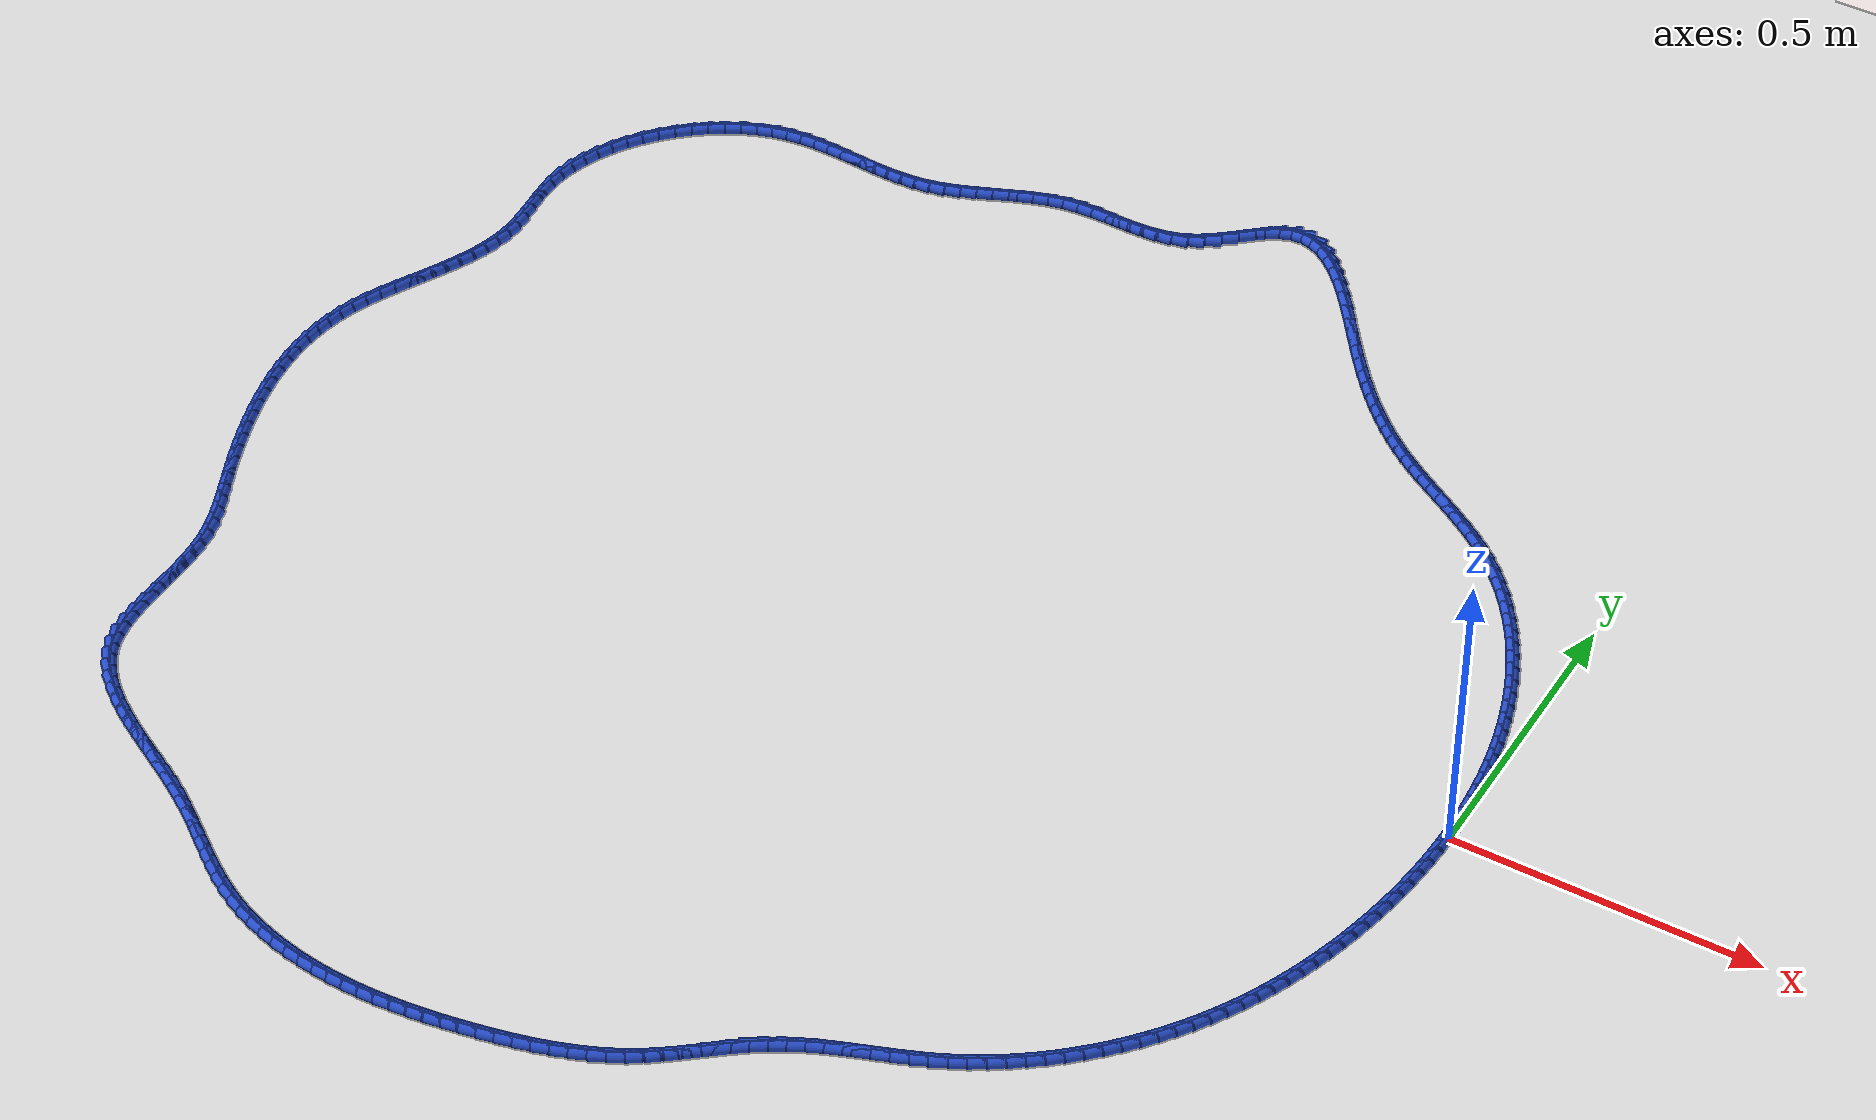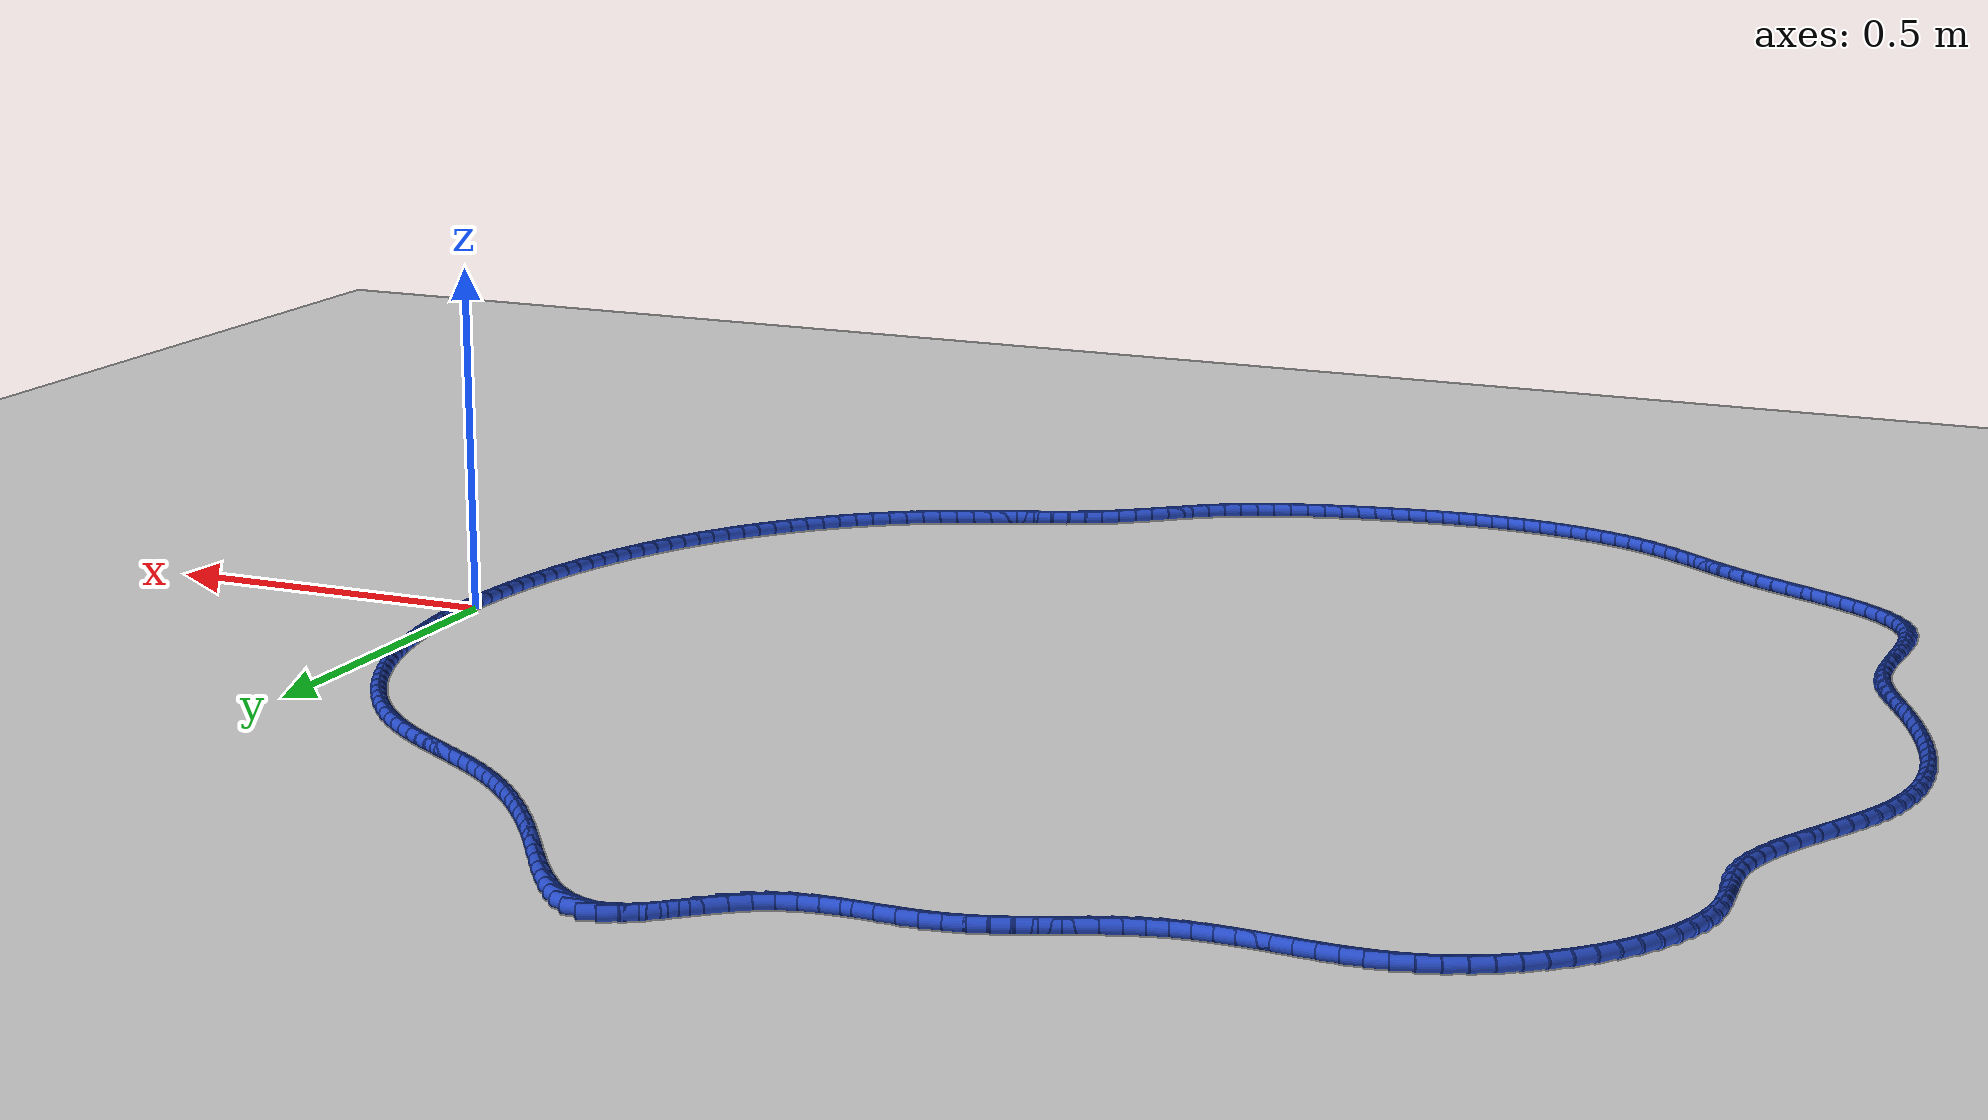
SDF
<sdf version="1.6">
 <world name="default">
  <light name="sun" type="directional">
   <pose>0 0 10 0 -0 0</pose>
   <diffuse>0.8 0.8 0.8 1</diffuse>
   <specular>0.2 0.2 0.2 1</specular>
   <attenuation>
    <range>1000</range>
    <constant>0.9</constant>
    <linear>0.01</linear>
    <quadratic>0.001</quadratic>
   </attenuation>
   <direction>-0.5 0.1 -0.9</direction>
  </light>
  <model name="ground_plane">
   <static>1</static>
   <link name="link">
    <collision name="collision">
     <geometry><plane><normal>0 0 1</normal><size>100 100</size></plane></geometry>
     <surface><friction><ode><mu>100</mu><mu2>50</mu2></ode></friction></surface>
    </collision>
    <visual name="visual">
     <cast_shadows>0</cast_shadows>
     <geometry><plane><normal>0 0 1</normal><size>100 100</size></plane></geometry>
     <material>
      <script><uri>file://media/materials/scripts/gazebo.material</uri><name>Gazebo/WhiteGlow</name></script>
     </material>
    </visual>
   </link>
  </model>
  <gravity>0 0 -9.8</gravity>
  <magnetic_field>6e-06 2.3e-05 -4.2e-05</magnetic_field>
  <atmosphere type="adiabatic"/>
  <physics name="default_physics" default="0" type="ode">
   <max_step_size>0.001</max_step_size>
   <real_time_factor>1</real_time_factor>
   <real_time_update_rate>1000</real_time_update_rate>
  </physics>
  <scene><ambient>0.4 0.4 0.4 1</ambient><background>0.7 0.7 0.7 1</background><shadows>1</shadows></scene>
  <spherical_coordinates>
   <surface_model>EARTH_WGS84</surface_model>
   <latitude_deg>0</latitude_deg>
   <longitude_deg>0</longitude_deg>
   <elevation>0</elevation>
   <heading_deg>0</heading_deg>
  </spherical_coordinates>
  <model name="line">
   <link name="link_0">
    <pose>-1.3010426069826053e-17 -1.1102230246251565e-16 0.01 0 1.57 -1.5650336162759861</pose>
    <collision name="collision">
     <geometry><cylinder><radius>0.01</radius><length>0.08</length></cylinder></geometry>
    </collision>
    <visual name="visual">
     <material>
      <script><name>Gazebo/Blue</name><uri>file://media/materials/scripts/gazebo.material</uri></script>
     </material>
     <geometry><cylinder><radius>0.01</radius><length>0.08</length></cylinder></geometry>
    </visual>
   </link>
   <link name="link_1">
    <pose>-0.00015394781854984716 0.02671418491323485 0.01 0 1.57 -1.5384784487555527</pose>
    <collision name="collision">
     <geometry><cylinder><radius>0.01</radius><length>0.08</length></cylinder></geometry>
    </collision>
    <visual name="visual">
     <material>
      <script><name>Gazebo/Blue</name><uri>file://media/materials/scripts/gazebo.material</uri></script>
     </material>
     <geometry><cylinder><radius>0.01</radius><length>0.08</length></cylinder></geometry>
    </visual>
   </link>
   <link name="link_2">
    <pose>-0.0010168731685485336 0.05340606431002454 0.01 0 1.57 -1.5110991230828021</pose>
    <collision name="collision">
     <geometry><cylinder><radius>0.01</radius><length>0.08</length></cylinder></geometry>
    </collision>
    <visual name="visual">
     <material>
      <script><name>Gazebo/Blue</name><uri>file://media/materials/scripts/gazebo.material</uri></script>
     </material>
     <geometry><cylinder><radius>0.01</radius><length>0.08</length></cylinder></geometry>
    </visual>
   </link>
   <link name="link_3">
    <pose>-0.0026101452453956065 0.08006357672868039 0.01 0 1.57 -1.482902638969219</pose>
    <collision name="collision">
     <geometry><cylinder><radius>0.01</radius><length>0.08</length></cylinder></geometry>
    </collision>
    <visual name="visual">
     <material>
      <script><name>Gazebo/Blue</name><uri>file://media/materials/scripts/gazebo.material</uri></script>
     </material>
     <geometry><cylinder><radius>0.01</radius><length>0.08</length></cylinder></geometry>
    </visual>
   </link>
   <link name="link_4">
    <pose>-0.004955133244490608 0.10667466070751394 0.01 0 1.57 -1.4539016090968433</pose>
    <collision name="collision">
     <geometry><cylinder><radius>0.01</radius><length>0.08</length></cylinder></geometry>
    </collision>
    <visual name="visual">
     <material>
      <script><name>Gazebo/Blue</name><uri>file://media/materials/scripts/gazebo.material</uri></script>
     </material>
     <geometry><cylinder><radius>0.01</radius><length>0.08</length></cylinder></geometry>
    </visual>
   </link>
   <link name="link_5">
    <pose>-0.008073206361233065 0.13322725478483652 0.01 0 1.57 -1.42411477450039</pose>
    <collision name="collision">
     <geometry><cylinder><radius>0.01</radius><length>0.08</length></cylinder></geometry>
    </collision>
    <visual name="visual">
     <material>
      <script><name>Gazebo/Blue</name><uri>file://media/materials/scripts/gazebo.material</uri></script>
     </material>
     <geometry><cylinder><radius>0.01</radius><length>0.08</length></cylinder></geometry>
    </visual>
   </link>
   <link name="link_6">
    <pose>-0.011985733791022524 0.15970929749895976 0.01 0 1.57 -1.3935674610541722</pose>
    <collision name="collision">
     <geometry><cylinder><radius>0.01</radius><length>0.08</length></cylinder></geometry>
    </collision>
    <visual name="visual">
     <material>
      <script><name>Gazebo/Blue</name><uri>file://media/materials/scripts/gazebo.material</uri></script>
     </material>
     <geometry><cylinder><radius>0.01</radius><length>0.08</length></cylinder></geometry>
    </visual>
   </link>
   <link name="link_7">
    <pose>-0.016714084729258505 0.18610872738819487 0.01 0 1.57 -1.3622919516019611</pose>
    <collision name="collision">
     <geometry><cylinder><radius>0.01</radius><length>0.08</length></cylinder></geometry>
    </collision>
    <visual name="visual">
     <material>
      <script><name>Gazebo/Blue</name><uri>file://media/materials/scripts/gazebo.material</uri></script>
     </material>
     <geometry><cylinder><radius>0.01</radius><length>0.08</length></cylinder></geometry>
    </visual>
   </link>
   <link name="link_8">
    <pose>-0.022279628371340565 0.21241348299085358 0.01 0 1.57 -1.330327747234454</pose>
    <collision name="collision">
     <geometry><cylinder><radius>0.01</radius><length>0.08</length></cylinder></geometry>
    </collision>
    <visual name="visual">
     <material>
      <script><name>Gazebo/Blue</name><uri>file://media/materials/scripts/gazebo.material</uri></script>
     </material>
     <geometry><cylinder><radius>0.01</radius><length>0.08</length></cylinder></geometry>
    </visual>
   </link>
   <link name="link_9">
    <pose>-0.02870373391266822 0.23861150284524713 0.01 0 1.57 -1.2977178127041347</pose>
    <collision name="collision">
     <geometry><cylinder><radius>0.01</radius><length>0.08</length></cylinder></geometry>
    </collision>
    <visual name="visual">
     <material>
      <script><name>Gazebo/Blue</name><uri>file://media/materials/scripts/gazebo.material</uri></script>
     </material>
     <geometry><cylinder><radius>0.01</radius><length>0.08</length></cylinder></geometry>
    </visual>
   </link>
   <link name="link_10">
    <pose>-0.036007256895986293 0.2646885019854826 0.01 0 1.57 -1.2644138853128541</pose>
    <collision name="collision">
     <geometry><cylinder><radius>0.01</radius><length>0.08</length></cylinder></geometry>
    </collision>
    <visual name="visual">
     <material>
      <script><name>Gazebo/Blue</name><uri>file://media/materials/scripts/gazebo.material</uri></script>
     </material>
     <geometry><cylinder><radius>0.01</radius><length>0.08</length></cylinder></geometry>
    </visual>
   </link>
   <link name="link_11">
    <pose>-0.04420378079151405 0.29059871603309645 0.01 0 1.57 -1.2302507836768217</pose>
    <collision name="collision">
     <geometry><cylinder><radius>0.01</radius><length>0.08</length></cylinder></geometry>
    </collision>
    <visual name="visual">
     <material>
      <script><name>Gazebo/Blue</name><uri>file://media/materials/scripts/gazebo.material</uri></script>
     </material>
     <geometry><cylinder><radius>0.01</radius><length>0.08</length></cylinder></geometry>
    </visual>
   </link>
   <link name="link_12">
    <pose>-0.05330149532814814 0.3162730321339608 0.01 0 1.57 -1.1950746123892246</pose>
    <collision name="collision">
     <geometry><cylinder><radius>0.01</radius><length>0.08</length></cylinder></geometry>
    </collision>
    <visual name="visual">
     <material>
      <script><name>Gazebo/Blue</name><uri>file://media/materials/scripts/gazebo.material</uri></script>
     </material>
     <geometry><cylinder><radius>0.01</radius><length>0.08</length></cylinder></geometry>
    </visual>
   </link>
   <link name="link_13">
    <pose>-0.06330846279405351 0.341641785767369 0.01 0 1.57 -1.158734699838362</pose>
    <collision name="collision">
     <geometry><cylinder><radius>0.01</radius><length>0.08</length></cylinder></geometry>
    </collision>
    <visual name="visual">
     <material>
      <script><name>Gazebo/Blue</name><uri>file://media/materials/scripts/gazebo.material</uri></script>
     </material>
     <geometry><cylinder><radius>0.01</radius><length>0.08</length></cylinder></geometry>
    </visual>
   </link>
   <link name="link_14">
    <pose>-0.07423274547739507 0.3666353124126141 0.01 0 1.57 -1.1210831322339245</pose>
    <collision name="collision">
     <geometry><cylinder><radius>0.01</radius><length>0.08</length></cylinder></geometry>
    </collision>
    <visual name="visual">
     <material>
      <script><name>Gazebo/Blue</name><uri>file://media/materials/scripts/gazebo.material</uri></script>
     </material>
     <geometry><cylinder><radius>0.01</radius><length>0.08</length></cylinder></geometry>
    </visual>
   </link>
   <link name="link_15">
    <pose>-0.08608240566633785 0.39118394754898955 0.01 0 1.57 -1.081975906738686</pose>
    <collision name="collision">
     <geometry><cylinder><radius>0.01</radius><length>0.08</length></cylinder></geometry>
    </collision>
    <visual name="visual">
     <material>
      <script><name>Gazebo/Blue</name><uri>file://media/materials/scripts/gazebo.material</uri></script>
     </material>
     <geometry><cylinder><radius>0.01</radius><length>0.08</length></cylinder></geometry>
    </visual>
   </link>
   <link name="link_16">
    <pose>-0.09886550564904673 0.4152180266557885 0.01 0 1.57 -1.0412748395296416</pose>
    <collision name="collision">
     <geometry><cylinder><radius>0.01</radius><length>0.08</length></cylinder></geometry>
    </collision>
    <visual name="visual">
     <material>
      <script><name>Gazebo/Blue</name><uri>file://media/materials/scripts/gazebo.material</uri></script>
     </material>
     <geometry><cylinder><radius>0.01</radius><length>0.08</length></cylinder></geometry>
    </visual>
   </link>
   <link name="link_17">
    <pose>-0.1125901077136867 0.4386678852123042 0.01 0 1.57 -0.9988503320855717</pose>
    <collision name="collision">
     <geometry><cylinder><radius>0.01</radius><length>0.08</length></cylinder></geometry>
    </collision>
    <visual name="visual">
     <material>
      <script><name>Gazebo/Blue</name><uri>file://media/materials/scripts/gazebo.material</uri></script>
     </material>
     <geometry><cylinder><radius>0.01</radius><length>0.08</length></cylinder></geometry>
    </visual>
   </link>
   <link name="link_18">
    <pose>-0.12726427414842273 0.46146385869782985 0.01 0 1.57 -0.9545850886975823</pose>
    <collision name="collision">
     <geometry><cylinder><radius>0.01</radius><length>0.08</length></cylinder></geometry>
    </collision>
    <visual name="visual">
     <material>
      <script><name>Gazebo/Blue</name><uri>file://media/materials/scripts/gazebo.material</uri></script>
     </material>
     <geometry><cylinder><radius>0.01</radius><length>0.08</length></cylinder></geometry>
    </visual>
   </link>
   <link name="link_19">
    <pose>-0.14289606724141962 0.4835362825916587 0.01 0 1.57 -0.9083788448806125</pose>
    <collision name="collision">
     <geometry><cylinder><radius>0.01</radius><length>0.08</length></cylinder></geometry>
    </collision>
    <visual name="visual">
     <material>
      <script><name>Gazebo/Blue</name><uri>file://media/materials/scripts/gazebo.material</uri></script>
     </material>
     <geometry><cylinder><radius>0.01</radius><length>0.08</length></cylinder></geometry>
    </visual>
   </link>
   <link name="link_20">
    <pose>-0.15949354928084256 0.5048154923730842 0.01 0 1.57 -0.8601541011872473</pose>
    <collision name="collision">
     <geometry><cylinder><radius>0.01</radius><length>0.08</length></cylinder></geometry>
    </collision>
    <visual name="visual">
     <material>
      <script><name>Gazebo/Blue</name><uri>file://media/materials/scripts/gazebo.material</uri></script>
     </material>
     <geometry><cylinder><radius>0.01</radius><length>0.08</length></cylinder></geometry>
    </visual>
   </link>
   <link name="link_21">
    <pose>-0.1770647825548563 0.5252318235213993 0.01 0 1.57 -0.8098627516726841</pose>
    <collision name="collision">
     <geometry><cylinder><radius>0.01</radius><length>0.08</length></cylinder></geometry>
    </collision>
    <visual name="visual">
     <material>
      <script><name>Gazebo/Blue</name><uri>file://media/materials/scripts/gazebo.material</uri></script>
     </material>
     <geometry><cylinder><radius>0.01</radius><length>0.08</length></cylinder></geometry>
    </visual>
   </link>
   <link name="link_22">
    <pose>-0.1956178293516259 0.5447156115158975 0.01 0 1.57 -0.7574933464994904</pose>
    <collision name="collision">
     <geometry><cylinder><radius>0.01</radius><length>0.08</length></cylinder></geometry>
    </collision>
    <visual name="visual">
     <material>
      <script><name>Gazebo/Blue</name><uri>file://media/materials/scripts/gazebo.material</uri></script>
     </material>
     <geometry><cylinder><radius>0.01</radius><length>0.08</length></cylinder></geometry>
    </visual>
   </link>
   <link name="link_23">
    <pose>-0.21516075195931628 0.5631971918358719 0.01 0 1.57 -0.703251048823187</pose>
    <collision name="collision">
     <geometry><cylinder><radius>0.01</radius><length>0.08</length></cylinder></geometry>
    </collision>
    <visual name="visual">
     <material>
      <script><name>Gazebo/Blue</name><uri>file://media/materials/scripts/gazebo.material</uri></script>
     </material>
     <geometry><cylinder><radius>0.01</radius><length>0.08</length></cylinder></geometry>
    </visual>
   </link>
   <link name="link_24">
    <pose>-0.23569851029058497 0.5806103595339971 0.01 0 1.57 -0.6528084806481628</pose>
    <collision name="collision">
     <geometry><cylinder><radius>0.01</radius><length>0.08</length></cylinder></geometry>
    </collision>
    <visual name="visual">
     <material>
      <script><name>Gazebo/Blue</name><uri>file://media/materials/scripts/gazebo.material</uri></script>
     </material>
     <geometry><cylinder><radius>0.01</radius><length>0.08</length></cylinder></geometry>
    </visual>
   </link>
   <link name="link_25">
    <pose>-0.2571349664023615 0.5970016476115715 0.01 0 1.57 -0.6127966086896626</pose>
    <collision name="collision">
     <geometry><cylinder><radius>0.01</radius><length>0.08</length></cylinder></geometry>
    </collision>
    <visual name="visual">
     <material>
      <script><name>Gazebo/Blue</name><uri>file://media/materials/scripts/gazebo.material</uri></script>
     </material>
     <geometry><cylinder><radius>0.01</radius><length>0.08</length></cylinder></geometry>
    </visual>
   </link>
   <link name="link_26">
    <pose>-0.2792529399344604 0.6125525679347155 0.01 0 1.57 -0.5833853333720594</pose>
    <collision name="collision">
     <geometry><cylinder><radius>0.01</radius><length>0.08</length></cylinder></geometry>
    </collision>
    <visual name="visual">
     <material>
      <script><name>Gazebo/Blue</name><uri>file://media/materials/scripts/gazebo.material</uri></script>
     </material>
     <geometry><cylinder><radius>0.01</radius><length>0.08</length></cylinder></geometry>
    </visual>
   </link>
   <link name="link_27">
    <pose>-0.30182811865757897 0.6274525853799099 0.01 0 1.57 -0.5643649457483669</pose>
    <collision name="collision">
     <geometry><cylinder><radius>0.01</radius><length>0.08</length></cylinder></geometry>
    </collision>
    <visual name="visual">
     <material>
      <script><name>Gazebo/Blue</name><uri>file://media/materials/scripts/gazebo.material</uri></script>
     </material>
     <geometry><cylinder><radius>0.01</radius><length>0.08</length></cylinder></geometry>
    </visual>
   </link>
   <link name="link_28">
    <pose>-0.32463619034241514 0.6418911648236363 0.01 0 1.57 -0.5556375580480541</pose>
    <collision name="collision">
     <geometry><cylinder><radius>0.01</radius><length>0.08</length></cylinder></geometry>
    </collision>
    <visual name="visual">
     <material>
      <script><name>Gazebo/Blue</name><uri>file://media/materials/scripts/gazebo.material</uri></script>
     </material>
     <geometry><cylinder><radius>0.01</radius><length>0.08</length></cylinder></geometry>
    </visual>
   </link>
   <link name="link_29">
    <pose>-0.34745284275966637 0.656057771142376 0.01 0 1.57 -0.5572785229361761</pose>
    <collision name="collision">
     <geometry><cylinder><radius>0.01</radius><length>0.08</length></cylinder></geometry>
    </collision>
    <visual name="visual">
     <material>
      <script><name>Gazebo/Blue</name><uri>file://media/materials/scripts/gazebo.material</uri></script>
     </material>
     <geometry><cylinder><radius>0.01</radius><length>0.08</length></cylinder></geometry>
    </visual>
   </link>
   <link name="link_30">
    <pose>-0.3700537636800304 0.6701418692126103 0.01 0 1.57 -0.5695722332646925</pose>
    <collision name="collision">
     <geometry><cylinder><radius>0.01</radius><length>0.08</length></cylinder></geometry>
    </collision>
    <visual name="visual">
     <material>
      <script><name>Gazebo/Blue</name><uri>file://media/materials/scripts/gazebo.material</uri></script>
     </material>
     <geometry><cylinder><radius>0.01</radius><length>0.08</length></cylinder></geometry>
    </visual>
   </link>
   <link name="link_31">
    <pose>-0.39221464087420477 0.6843329239108202 0.01 0 1.57 -0.5930246397598444</pose>
    <collision name="collision">
     <geometry><cylinder><radius>0.01</radius><length>0.08</length></cylinder></geometry>
    </collision>
    <visual name="visual">
     <material>
      <script><name>Gazebo/Blue</name><uri>file://media/materials/scripts/gazebo.material</uri></script>
     </material>
     <geometry><cylinder><radius>0.01</radius><length>0.08</length></cylinder></geometry>
    </visual>
   </link>
   <link name="link_32">
    <pose>-0.413711162112887 0.6988204001134872 0.01 0 1.57 -0.6268626961544883</pose>
    <collision name="collision">
     <geometry><cylinder><radius>0.01</radius><length>0.08</length></cylinder></geometry>
    </collision>
    <visual name="visual">
     <material>
      <script><name>Gazebo/Blue</name><uri>file://media/materials/scripts/gazebo.material</uri></script>
     </material>
     <geometry><cylinder><radius>0.01</radius><length>0.08</length></cylinder></geometry>
    </visual>
   </link>
   <link name="link_33">
    <pose>-0.43436461234086965 0.7137801187358281 0.01 0 1.57 -0.6639068947519713</pose>
    <collision name="collision">
     <geometry><cylinder><radius>0.01</radius><length>0.08</length></cylinder></geometry>
    </collision>
    <visual name="visual">
     <material>
      <script><name>Gazebo/Blue</name><uri>file://media/materials/scripts/gazebo.material</uri></script>
     </material>
     <geometry><cylinder><radius>0.01</radius><length>0.08</length></cylinder></geometry>
    </visual>
   </link>
   <link name="link_34">
    <pose>-0.45422582177543663 0.7293192142696471 0.01 0 1.57 -0.7011860236053205</pose>
    <collision name="collision">
     <geometry><cylinder><radius>0.01</radius><length>0.08</length></cylinder></geometry>
    </collision>
    <visual name="visual">
     <material>
      <script><name>Gazebo/Blue</name><uri>file://media/materials/scripts/gazebo.material</uri></script>
     </material>
     <geometry><cylinder><radius>0.01</radius><length>0.08</length></cylinder></geometry>
    </visual>
   </link>
   <link name="link_35">
    <pose>-0.47341769411603757 0.7455232547869342 0.01 0 1.57 -0.7379361261699516</pose>
    <collision name="collision">
     <geometry><cylinder><radius>0.01</radius><length>0.08</length></cylinder></geometry>
    </collision>
    <visual name="visual">
     <material>
      <script><name>Gazebo/Blue</name><uri>file://media/materials/scripts/gazebo.material</uri></script>
     </material>
     <geometry><cylinder><radius>0.01</radius><length>0.08</length></cylinder></geometry>
    </visual>
   </link>
   <link name="link_36">
    <pose>-0.4920631588665579 0.7624778006382646 0.01 0 1.57 -0.773420285654574</pose>
    <collision name="collision">
     <geometry><cylinder><radius>0.01</radius><length>0.08</length></cylinder></geometry>
    </collision>
    <visual name="visual">
     <material>
      <script><name>Gazebo/Blue</name><uri>file://media/materials/scripts/gazebo.material</uri></script>
     </material>
     <geometry><cylinder><radius>0.01</radius><length>0.08</length></cylinder></geometry>
    </visual>
   </link>
   <link name="link_37">
    <pose>-0.5102851455308823 0.780268412174213 0.01 0 1.57 -0.8069814928297969</pose>
    <collision name="collision">
     <geometry><cylinder><radius>0.01</radius><length>0.08</length></cylinder></geometry>
    </collision>
    <visual name="visual">
     <material>
      <script><name>Gazebo/Blue</name><uri>file://media/materials/scripts/gazebo.material</uri></script>
     </material>
     <geometry><cylinder><radius>0.01</radius><length>0.08</length></cylinder></geometry>
    </visual>
   </link>
   <link name="link_38">
    <pose>-0.5282065836128967 0.7989806497453545 0.01 0 1.57 -0.8380838496791576</pose>
    <collision name="collision">
     <geometry><cylinder><radius>0.01</radius><length>0.08</length></cylinder></geometry>
    </collision>
    <visual name="visual">
     <material>
      <script><name>Gazebo/Blue</name><uri>file://media/materials/scripts/gazebo.material</uri></script>
     </material>
     <geometry><cylinder><radius>0.01</radius><length>0.08</length></cylinder></geometry>
    </visual>
   </link>
   <link name="link_39">
    <pose>-0.545950402616486 0.8187000737022639 0.01 0 1.57 -0.8663361741394966</pose>
    <collision name="collision">
     <geometry><cylinder><radius>0.01</radius><length>0.08</length></cylinder></geometry>
    </collision>
    <visual name="visual">
     <material>
      <script><name>Gazebo/Blue</name><uri>file://media/materials/scripts/gazebo.material</uri></script>
     </material>
     <geometry><cylinder><radius>0.01</radius><length>0.08</length></cylinder></geometry>
    </visual>
   </link>
   <link name="link_40">
    <pose>-0.5636395320455353 0.839512244395516 0.01 0 1.57 -0.8914973038364443</pose>
    <collision name="collision">
     <geometry><cylinder><radius>0.01</radius><length>0.08</length></cylinder></geometry>
    </collision>
    <visual name="visual">
     <material>
      <script><name>Gazebo/Blue</name><uri>file://media/materials/scripts/gazebo.material</uri></script>
     </material>
     <geometry><cylinder><radius>0.01</radius><length>0.08</length></cylinder></geometry>
    </visual>
   </link>
   <link name="link_41">
    <pose>-0.5813969014039301 0.8615027221756857 0.01 0 1.57 -0.9134660706380294</pose>
    <collision name="collision">
     <geometry><cylinder><radius>0.01</radius><length>0.08</length></cylinder></geometry>
    </collision>
    <visual name="visual">
     <material>
      <script><name>Gazebo/Blue</name><uri>file://media/materials/scripts/gazebo.material</uri></script>
     </material>
     <geometry><cylinder><radius>0.01</radius><length>0.08</length></cylinder></geometry>
    </visual>
   </link>
   <link name="link_42">
    <pose>-0.5993454401955556 0.884757067393348 0.01 0 1.57 -0.9322609290077131</pose>
    <collision name="collision">
     <geometry><cylinder><radius>0.01</radius><length>0.08</length></cylinder></geometry>
    </collision>
    <visual name="visual">
     <material>
      <script><name>Gazebo/Blue</name><uri>file://media/materials/scripts/gazebo.material</uri></script>
     </material>
     <geometry><cylinder><radius>0.01</radius><length>0.08</length></cylinder></geometry>
    </visual>
   </link>
   <link name="link_43">
    <pose>-0.6176080779242967 0.9093608403990776 0.01 0 1.57 -0.9467397063344808</pose>
    <collision name="collision">
     <geometry><cylinder><radius>0.01</radius><length>0.08</length></cylinder></geometry>
    </collision>
    <visual name="visual">
     <material>
      <script><name>Gazebo/Blue</name><uri>file://media/materials/scripts/gazebo.material</uri></script>
     </material>
     <geometry><cylinder><radius>0.01</radius><length>0.08</length></cylinder></geometry>
    </visual>
   </link>
   <link name="link_44">
    <pose>-0.636288941984302 0.9353046483178902 0.01 0 1.57 -0.9502564664584233</pose>
    <collision name="collision">
     <geometry><cylinder><radius>0.01</radius><length>0.08</length></cylinder></geometry>
    </collision>
    <visual name="visual">
     <material>
      <script><name>Gazebo/Blue</name><uri>file://media/materials/scripts/gazebo.material</uri></script>
     </material>
     <geometry><cylinder><radius>0.01</radius><length>0.08</length></cylinder></geometry>
    </visual>
   </link>
   <link name="link_45">
    <pose>-0.6553808357144055 0.9620168965707229 0.01 0 1.57 -0.9411535458029279</pose>
    <collision name="collision">
     <geometry><cylinder><radius>0.01</radius><length>0.08</length></cylinder></geometry>
    </collision>
    <visual name="visual">
     <material>
      <script><name>Gazebo/Blue</name><uri>file://media/materials/scripts/gazebo.material</uri></script>
     </material>
     <geometry><cylinder><radius>0.01</radius><length>0.08</length></cylinder></geometry>
    </visual>
   </link>
   <link name="link_46">
    <pose>-0.6748357425875617 0.9887198446732742 0.01 0 1.57 -0.9191186451030166</pose>
    <collision name="collision">
     <geometry><cylinder><radius>0.01</radius><length>0.08</length></cylinder></geometry>
    </collision>
    <visual name="visual">
     <material>
      <script><name>Gazebo/Blue</name><uri>file://media/materials/scripts/gazebo.material</uri></script>
     </material>
     <geometry><cylinder><radius>0.01</radius><length>0.08</length></cylinder></geometry>
    </visual>
   </link>
   <link name="link_47">
    <pose>-0.6946055842129266 1.0146354397205957 0.01 0 1.57 -0.8822733708095486</pose>
    <collision name="collision">
     <geometry><cylinder><radius>0.01</radius><length>0.08</length></cylinder></geometry>
    </collision>
    <visual name="visual">
     <material>
      <script><name>Gazebo/Blue</name><uri>file://media/materials/scripts/gazebo.material</uri></script>
     </material>
     <geometry><cylinder><radius>0.01</radius><length>0.08</length></cylinder></geometry>
    </visual>
   </link>
   <link name="link_48">
    <pose>-0.7146422821996548 1.0389856288077375 0.01 0 1.57 -0.826812303792043</pose>
    <collision name="collision">
     <geometry><cylinder><radius>0.01</radius><length>0.08</length></cylinder></geometry>
    </collision>
    <visual name="visual">
     <material>
      <script><name>Gazebo/Blue</name><uri>file://media/materials/scripts/gazebo.material</uri></script>
     </material>
     <geometry><cylinder><radius>0.01</radius><length>0.08</length></cylinder></geometry>
    </visual>
   </link>
   <link name="link_49">
    <pose>-0.7348977581569021 1.060992359029751 0.01 0 1.57 -0.7462194824212696</pose>
    <collision name="collision">
     <geometry><cylinder><radius>0.01</radius><length>0.08</length></cylinder></geometry>
    </collision>
    <visual name="visual">
     <material>
      <script><name>Gazebo/Blue</name><uri>file://media/materials/scripts/gazebo.material</uri></script>
     </material>
     <geometry><cylinder><radius>0.01</radius><length>0.08</length></cylinder></geometry>
    </visual>
   </link>
   <link name="link_50">
    <pose>-0.7553239336938238 1.0798775774816864 0.01 0 1.57 -0.6301024117576631</pose>
    <collision name="collision">
     <geometry><cylinder><radius>0.01</radius><length>0.08</length></cylinder></geometry>
    </collision>
    <visual name="visual">
     <material>
      <script><name>Gazebo/Blue</name><uri>file://media/materials/scripts/gazebo.material</uri></script>
     </material>
     <geometry><cylinder><radius>0.01</radius><length>0.08</length></cylinder></geometry>
    </visual>
   </link>
   <link name="link_51">
    <pose>-0.7758727304195749 1.094863231258595 0.01 0 1.57 -0.46350664944377673</pose>
    <collision name="collision">
     <geometry><cylinder><radius>0.01</radius><length>0.08</length></cylinder></geometry>
    </collision>
    <visual name="visual">
     <material>
      <script><name>Gazebo/Blue</name><uri>file://media/materials/scripts/gazebo.material</uri></script>
     </material>
     <geometry><cylinder><radius>0.01</radius><length>0.08</length></cylinder></geometry>
    </visual>
   </link>
   <link name="link_52">
    <pose>-0.7964960699433113 1.1051712674555274 0.01 0 1.57 -0.23079643906061223</pose>
    <collision name="collision">
     <geometry><cylinder><radius>0.01</radius><length>0.08</length></cylinder></geometry>
    </collision>
    <visual name="visual">
     <material>
      <script><name>Gazebo/Blue</name><uri>file://media/materials/scripts/gazebo.material</uri></script>
     </material>
     <geometry><cylinder><radius>0.01</radius><length>0.08</length></cylinder></geometry>
    </visual>
   </link>
   <link name="link_53">
    <pose>-0.8171458738741879 1.1100236331675346 0.01 0 1.57 0.06686473382247758</pose>
    <collision name="collision">
     <geometry><cylinder><radius>0.01</radius><length>0.08</length></cylinder></geometry>
    </collision>
    <visual name="visual">
     <material>
      <script><name>Gazebo/Blue</name><uri>file://media/materials/scripts/gazebo.material</uri></script>
     </material>
     <geometry><cylinder><radius>0.01</radius><length>0.08</length></cylinder></geometry>
    </visual>
   </link>
   <link name="link_54">
    <pose>-0.8377740638213603 1.1086422754896672 0.01 0 1.57 0.37661075256918597</pose>
    <collision name="collision">
     <geometry><cylinder><radius>0.01</radius><length>0.08</length></cylinder></geometry>
    </collision>
    <visual name="visual">
     <material>
      <script><name>Gazebo/Blue</name><uri>file://media/materials/scripts/gazebo.material</uri></script>
     </material>
     <geometry><cylinder><radius>0.01</radius><length>0.08</length></cylinder></geometry>
    </visual>
   </link>
   <link name="link_55">
    <pose>-0.8583561243334903 1.1005023158253229 0.01 0 1.57 0.5843828397875431</pose>
    <collision name="collision">
     <geometry><cylinder><radius>0.01</radius><length>0.08</length></cylinder></geometry>
    </collision>
    <visual name="visual">
     <material>
      <script><name>Gazebo/Blue</name><uri>file://media/materials/scripts/gazebo.material</uri></script>
     </material>
     <geometry><cylinder><radius>0.01</radius><length>0.08</length></cylinder></geometry>
    </visual>
   </link>
   <link name="link_56">
    <pose>-0.8790302738250624 1.0868273855171218 0.01 0 1.57 0.6882450072943948</pose>
    <collision name="collision">
     <geometry><cylinder><radius>0.01</radius><length>0.08</length></cylinder></geometry>
    </collision>
    <visual name="visual">
     <material>
      <script><name>Gazebo/Blue</name><uri>file://media/materials/scripts/gazebo.material</uri></script>
     </material>
     <geometry><cylinder><radius>0.01</radius><length>0.08</length></cylinder></geometry>
    </visual>
   </link>
   <link name="link_57">
    <pose>-0.9000034309787839 1.0695792726595492 0.01 0 1.57 0.7204752794274424</pose>
    <collision name="collision">
     <geometry><cylinder><radius>0.01</radius><length>0.08</length></cylinder></geometry>
    </collision>
    <visual name="visual">
     <material>
      <script><name>Gazebo/Blue</name><uri>file://media/materials/scripts/gazebo.material</uri></script>
     </material>
     <geometry><cylinder><radius>0.01</radius><length>0.08</length></cylinder></geometry>
    </visual>
   </link>
   <link name="link_58">
    <pose>-0.921482757422946 1.0507223756996864 0.01 0 1.57 0.6949350696536066</pose>
    <collision name="collision">
     <geometry><cylinder><radius>0.01</radius><length>0.08</length></cylinder></geometry>
    </collision>
    <visual name="visual">
     <material>
      <script><name>Gazebo/Blue</name><uri>file://media/materials/scripts/gazebo.material</uri></script>
     </material>
     <geometry><cylinder><radius>0.01</radius><length>0.08</length></cylinder></geometry>
    </visual>
   </link>
   <link name="link_59">
    <pose>-0.9436754147858407 1.0322210930846158 0.01 0 1.57 0.6107859203684222</pose>
    <collision name="collision">
     <geometry><cylinder><radius>0.01</radius><length>0.08</length></cylinder></geometry>
    </collision>
    <visual name="visual">
     <material>
      <script><name>Gazebo/Blue</name><uri>file://media/materials/scripts/gazebo.material</uri></script>
     </material>
     <geometry><cylinder><radius>0.01</radius><length>0.08</length></cylinder></geometry>
    </visual>
   </link>
   <link name="link_60">
    <pose>-0.96678856469576 1.0160398232614203 0.01 0 1.57 0.4603137982510625</pose>
    <collision name="collision">
     <geometry><cylinder><radius>0.01</radius><length>0.08</length></cylinder></geometry>
    </collision>
    <visual name="visual">
     <material>
      <script><name>Gazebo/Blue</name><uri>file://media/materials/scripts/gazebo.material</uri></script>
     </material>
     <geometry><cylinder><radius>0.01</radius><length>0.08</length></cylinder></geometry>
    </visual>
   </link>
   <link name="link_61">
    <pose>-0.9910126477394421 1.0040285622569287 0.01 0 1.57 0.2916671352981252</pose>
    <collision name="collision">
     <geometry><cylinder><radius>0.01</radius><length>0.08</length></cylinder></geometry>
    </collision>
    <visual name="visual">
     <material>
      <script><name>Gazebo/Blue</name><uri>file://media/materials/scripts/gazebo.material</uri></script>
     </material>
     <geometry><cylinder><radius>0.01</radius><length>0.08</length></cylinder></geometry>
    </visual>
   </link>
   <link name="link_62">
    <pose>-1.0163039654575499 0.9964353679972839 0.01 0 1.57 0.1558032724814868</pose>
    <collision name="collision">
     <geometry><cylinder><radius>0.01</radius><length>0.08</length></cylinder></geometry>
    </collision>
    <visual name="visual">
     <material>
      <script><name>Gazebo/Blue</name><uri>file://media/materials/scripts/gazebo.material</uri></script>
     </material>
     <geometry><cylinder><radius>0.01</radius><length>0.08</length></cylinder></geometry>
    </visual>
   </link>
   <link name="link_63">
    <pose>-1.0424464535973896 0.9923290020193334 0.01 0 1.57 0.058876391674849204</pose>
    <collision name="collision">
     <geometry><cylinder><radius>0.01</radius><length>0.08</length></cylinder></geometry>
    </collision>
    <visual name="visual">
     <material>
      <script><name>Gazebo/Blue</name><uri>file://media/materials/scripts/gazebo.material</uri></script>
     </material>
     <geometry><cylinder><radius>0.01</radius><length>0.08</length></cylinder></geometry>
    </visual>
   </link>
   <link name="link_64">
    <pose>-1.069220046005786 0.9907508455619091 0.01 0 1.57 0.0003150934045366978</pose>
    <collision name="collision">
     <geometry><cylinder><radius>0.01</radius><length>0.08</length></cylinder></geometry>
    </collision>
    <visual name="visual">
     <material>
      <script><name>Gazebo/Blue</name><uri>file://media/materials/scripts/gazebo.material</uri></script>
     </material>
     <geometry><cylinder><radius>0.01</radius><length>0.08</length></cylinder></geometry>
    </visual>
   </link>
   <link name="link_65">
    <pose>-1.096404676529562 0.9907422798638428 0.01 0 1.57 -0.02200167445753424</pose>
    <collision name="collision">
     <geometry><cylinder><radius>0.01</radius><length>0.08</length></cylinder></geometry>
    </collision>
    <visual name="visual">
     <material>
      <script><name>Gazebo/Blue</name><uri>file://media/materials/scripts/gazebo.material</uri></script>
     </material>
     <geometry><cylinder><radius>0.01</radius><length>0.08</length></cylinder></geometry>
    </visual>
   </link>
   <link name="link_66">
    <pose>-1.123780279015543 0.9913446861639665 0.01 0 1.57 -0.009315710978553085</pose>
    <collision name="collision">
     <geometry><cylinder><radius>0.01</radius><length>0.08</length></cylinder></geometry>
    </collision>
    <visual name="visual">
     <material>
      <script><name>Gazebo/Blue</name><uri>file://media/materials/scripts/gazebo.material</uri></script>
     </material>
     <geometry><cylinder><radius>0.01</radius><length>0.08</length></cylinder></geometry>
    </visual>
   </link>
   <link name="link_67">
    <pose>-1.1511267873105522 0.9915994457011121 0.01 0 1.57 0.03878529648516115</pose>
    <collision name="collision">
     <geometry><cylinder><radius>0.01</radius><length>0.08</length></cylinder></geometry>
    </collision>
    <visual name="visual">
     <material>
      <script><name>Gazebo/Blue</name><uri>file://media/materials/scripts/gazebo.material</uri></script>
     </material>
     <geometry><cylinder><radius>0.01</radius><length>0.08</length></cylinder></geometry>
    </visual>
   </link>
   <link name="link_68">
    <pose>-1.1782241352614138 0.9905479397141118 0.01 0 1.57 0.12340733489830848</pose>
    <collision name="collision">
     <geometry><cylinder><radius>0.01</radius><length>0.08</length></cylinder></geometry>
    </collision>
    <visual name="visual">
     <material>
      <script><name>Gazebo/Blue</name><uri>file://media/materials/scripts/gazebo.material</uri></script>
     </material>
     <geometry><cylinder><radius>0.01</radius><length>0.08</length></cylinder></geometry>
    </visual>
   </link>
   <link name="link_69">
    <pose>-1.204855065224879 0.9872447018272346 0.01 0 1.57 0.22199528667618085</pose>
    <collision name="collision">
     <geometry><cylinder><radius>0.01</radius><length>0.08</length></cylinder></geometry>
    </collision>
    <visual name="visual">
     <material>
      <script><name>Gazebo/Blue</name><uri>file://media/materials/scripts/gazebo.material</uri></script>
     </material>
     <geometry><cylinder><radius>0.01</radius><length>0.08</length></cylinder></geometry>
    </visual>
   </link>
   <link name="link_70">
    <pose>-1.2309334606852995 0.9813584057965792 0.01 0 1.57 0.3004011627501246</pose>
    <collision name="collision">
     <geometry><cylinder><radius>0.01</radius><length>0.08</length></cylinder></geometry>
    </collision>
    <visual name="visual">
     <material>
      <script><name>Gazebo/Blue</name><uri>file://media/materials/scripts/gazebo.material</uri></script>
     </material>
     <geometry><cylinder><radius>0.01</radius><length>0.08</length></cylinder></geometry>
    </visual>
   </link>
   <link name="link_71">
    <pose>-1.2565574819972969 0.9734207027177864 0.01 0 1.57 0.35571955218539497</pose>
    <collision name="collision">
     <geometry><cylinder><radius>0.01</radius><length>0.08</length></cylinder></geometry>
    </collision>
    <visual name="visual">
     <material>
      <script><name>Gazebo/Blue</name><uri>file://media/materials/scripts/gazebo.material</uri></script>
     </material>
     <geometry><cylinder><radius>0.01</radius><length>0.08</length></cylinder></geometry>
    </visual>
   </link>
   <link name="link_72">
    <pose>-1.2818391121601214 0.9640279757880812 0.01 0 1.57 0.38842610063873384</pose>
    <collision name="collision">
     <geometry><cylinder><radius>0.01</radius><length>0.08</length></cylinder></geometry>
    </collision>
    <visual name="visual">
     <material>
      <script><name>Gazebo/Blue</name><uri>file://media/materials/scripts/gazebo.material</uri></script>
     </material>
     <geometry><cylinder><radius>0.01</radius><length>0.08</length></cylinder></geometry>
    </visual>
   </link>
   <link name="link_73">
    <pose>-1.3068903341730211 0.953776608204689 0.01 0 1.57 0.3990539690582409</pose>
    <collision name="collision">
     <geometry><cylinder><radius>0.01</radius><length>0.08</length></cylinder></geometry>
    </collision>
    <visual name="visual">
     <material>
      <script><name>Gazebo/Blue</name><uri>file://media/materials/scripts/gazebo.material</uri></script>
     </material>
     <geometry><cylinder><radius>0.01</radius><length>0.08</length></cylinder></geometry>
    </visual>
   </link>
   <link name="link_74">
    <pose>-1.3318231310352473 0.9432629831648351 0.01 0 1.57 0.38771213907537416</pose>
    <collision name="collision">
     <geometry><cylinder><radius>0.01</radius><length>0.08</length></cylinder></geometry>
    </collision>
    <visual name="visual">
     <material>
      <script><name>Gazebo/Blue</name><uri>file://media/materials/scripts/gazebo.material</uri></script>
     </material>
     <geometry><cylinder><radius>0.01</radius><length>0.08</length></cylinder></geometry>
    </visual>
   </link>
   <link name="link_75">
    <pose>-1.356749485746048 0.9330834838657444 0.01 0 1.57 0.3539296841890463</pose>
    <collision name="collision">
     <geometry><cylinder><radius>0.01</radius><length>0.08</length></cylinder></geometry>
    </collision>
    <visual name="visual">
     <material>
      <script><name>Gazebo/Blue</name><uri>file://media/materials/scripts/gazebo.material</uri></script>
     </material>
     <geometry><cylinder><radius>0.01</radius><length>0.08</length></cylinder></geometry>
    </visual>
   </link>
   <link name="link_76">
    <pose>-1.3817813813046744 0.9238344935046431 0.01 0 1.57 0.2967992722373064</pose>
    <collision name="collision">
     <geometry><cylinder><radius>0.01</radius><length>0.08</length></cylinder></geometry>
    </collision>
    <visual name="visual">
     <material>
      <script><name>Gazebo/Blue</name><uri>file://media/materials/scripts/gazebo.material</uri></script>
     </material>
     <geometry><cylinder><radius>0.01</radius><length>0.08</length></cylinder></geometry>
    </visual>
   </link>
   <link name="link_77">
    <pose>-1.4070308007103747 0.9161123952787552 0.01 0 1.57 0.21551840734850633</pose>
    <collision name="collision">
     <geometry><cylinder><radius>0.01</radius><length>0.08</length></cylinder></geometry>
    </collision>
    <visual name="visual">
     <material>
      <script><name>Gazebo/Blue</name><uri>file://media/materials/scripts/gazebo.material</uri></script>
     </material>
     <geometry><cylinder><radius>0.01</radius><length>0.08</length></cylinder></geometry>
    </visual>
   </link>
   <link name="link_78">
    <pose>-1.4326095905813583 0.9105127274320154 0.01 0 1.57 0.12146366894105301</pose>
    <collision name="collision">
     <geometry><cylinder><radius>0.01</radius><length>0.08</length></cylinder></geometry>
    </collision>
    <visual name="visual">
     <material>
      <script><name>Gazebo/Blue</name><uri>file://media/materials/scripts/gazebo.material</uri></script>
     </material>
     <geometry><cylinder><radius>0.01</radius><length>0.08</length></cylinder></geometry>
    </visual>
   </link>
   <link name="link_79">
    <pose>-1.4585829941870856 0.9073422956045123 0.01 0 1.57 0.043409096063745684</pose>
    <collision name="collision">
     <geometry><cylinder><radius>0.01</radius><length>0.08</length></cylinder></geometry>
    </collision>
    <visual name="visual">
     <material>
      <script><name>Gazebo/Blue</name><uri>file://media/materials/scripts/gazebo.material</uri></script>
     </material>
     <geometry><cylinder><radius>0.01</radius><length>0.08</length></cylinder></geometry>
    </visual>
   </link>
   <link name="link_80">
    <pose>-1.484901848881031 0.9061990997623764 0.01 0 1.57 -0.014107302118341374</pose>
    <collision name="collision">
     <geometry><cylinder><radius>0.01</radius><length>0.08</length></cylinder></geometry>
    </collision>
    <visual name="visual">
     <material>
      <script><name>Gazebo/Blue</name><uri>file://media/materials/scripts/gazebo.material</uri></script>
     </material>
     <geometry><cylinder><radius>0.01</radius><length>0.08</length></cylinder></geometry>
    </visual>
   </link>
   <link name="link_81">
    <pose>-1.5114997553226421 0.9065743493581484 0.01 0 1.57 -0.05160931934277523</pose>
    <collision name="collision">
     <geometry><cylinder><radius>0.01</radius><length>0.08</length></cylinder></geometry>
    </collision>
    <visual name="visual">
     <material>
      <script><name>Gazebo/Blue</name><uri>file://media/materials/scripts/gazebo.material</uri></script>
     </material>
     <geometry><cylinder><radius>0.01</radius><length>0.08</length></cylinder></geometry>
    </visual>
   </link>
   <link name="link_82">
    <pose>-1.5383103141713659 0.9079592538443689 0.01 0 1.57 -0.06984140740538196</pose>
    <collision name="collision">
     <geometry><cylinder><radius>0.01</radius><length>0.08</length></cylinder></geometry>
    </collision>
    <visual name="visual">
     <material>
      <script><name>Gazebo/Blue</name><uri>file://media/materials/scripts/gazebo.material</uri></script>
     </material>
     <geometry><cylinder><radius>0.01</radius><length>0.08</length></cylinder></geometry>
    </visual>
   </link>
   <link name="link_83">
    <pose>-1.56526712608665 0.9098450226735788 0.01 0 1.57 -0.06934404394226333</pose>
    <collision name="collision">
     <geometry><cylinder><radius>0.01</radius><length>0.08</length></cylinder></geometry>
    </collision>
    <visual name="visual">
     <material>
      <script><name>Gazebo/Blue</name><uri>file://media/materials/scripts/gazebo.material</uri></script>
     </material>
     <geometry><cylinder><radius>0.01</radius><length>0.08</length></cylinder></geometry>
    </visual>
   </link>
   <link name="link_84">
    <pose>-1.5923037917279426 0.9117228652983193 0.01 0 1.57 -0.050276258954411256</pose>
    <collision name="collision">
     <geometry><cylinder><radius>0.01</radius><length>0.08</length></cylinder></geometry>
    </collision>
    <visual name="visual">
     <material>
      <script><name>Gazebo/Blue</name><uri>file://media/materials/scripts/gazebo.material</uri></script>
     </material>
     <geometry><cylinder><radius>0.01</radius><length>0.08</length></cylinder></geometry>
    </visual>
   </link>
   <link name="link_85">
    <pose>-1.6193539117546907 0.9130839911711308 0.01 0 1.57 -0.012430977860833359</pose>
    <collision name="collision">
     <geometry><cylinder><radius>0.01</radius><length>0.08</length></cylinder></geometry>
    </collision>
    <visual name="visual">
     <material>
      <script><name>Gazebo/Blue</name><uri>file://media/materials/scripts/gazebo.material</uri></script>
     </material>
     <geometry><cylinder><radius>0.01</radius><length>0.08</length></cylinder></geometry>
    </visual>
   </link>
   <link name="link_86">
    <pose>-1.6463510868263416 0.913419609744554 0.01 0 1.57 0.044567790368423385</pose>
    <collision name="collision">
     <geometry><cylinder><radius>0.01</radius><length>0.08</length></cylinder></geometry>
    </collision>
    <visual name="visual">
     <material>
      <script><name>Gazebo/Blue</name><uri>file://media/materials/scripts/gazebo.material</uri></script>
     </material>
     <geometry><cylinder><radius>0.01</radius><length>0.08</length></cylinder></geometry>
    </visual>
   </link>
   <link name="link_87">
    <pose>-1.6732289176023436 0.9122209304711305 0.01 0 1.57 0.12085860153493712</pose>
    <collision name="collision">
     <geometry><cylinder><radius>0.01</radius><length>0.08</length></cylinder></geometry>
    </collision>
    <visual name="visual">
     <material>
      <script><name>Gazebo/Blue</name><uri>file://media/materials/scripts/gazebo.material</uri></script>
     </material>
     <geometry><cylinder><radius>0.01</radius><length>0.08</length></cylinder></geometry>
    </visual>
   </link>
   <link name="link_88">
    <pose>-1.6999210047421442 0.908979162803401 0.01 0 1.57 0.21554308193683752</pose>
    <collision name="collision">
     <geometry><cylinder><radius>0.01</radius><length>0.08</length></cylinder></geometry>
    </collision>
    <visual name="visual">
     <material>
      <script><name>Gazebo/Blue</name><uri>file://media/materials/scripts/gazebo.material</uri></script>
     </material>
     <geometry><cylinder><radius>0.01</radius><length>0.08</length></cylinder></geometry>
    </visual>
   </link>
   <link name="link_89">
    <pose>-1.72636008425299 0.9031904780797305 0.01 0 1.57 0.31759753539288654</pose>
    <collision name="collision">
     <geometry><cylinder><radius>0.01</radius><length>0.08</length></cylinder></geometry>
    </collision>
    <visual name="visual">
     <material>
      <script><name>Gazebo/Blue</name><uri>file://media/materials/scripts/gazebo.material</uri></script>
     </material>
     <geometry><cylinder><radius>0.01</radius><length>0.08</length></cylinder></geometry>
    </visual>
   </link>
   <link name="link_90">
    <pose>-1.7524320296979632 0.8946199720651433 0.01 0 1.57 0.41309471905929546</pose>
    <collision name="collision">
     <geometry><cylinder><radius>0.01</radius><length>0.08</length></cylinder></geometry>
    </collision>
    <visual name="visual">
     <material>
      <script><name>Gazebo/Blue</name><uri>file://media/materials/scripts/gazebo.material</uri></script>
     </material>
     <geometry><cylinder><radius>0.01</radius><length>0.08</length></cylinder></geometry>
    </visual>
   </link>
   <link name="link_91">
    <pose>-1.777952824363797 0.8834338122747923 0.01 0 1.57 0.5020362140405702</pose>
    <collision name="collision">
     <geometry><cylinder><radius>0.01</radius><length>0.08</length></cylinder></geometry>
    </collision>
    <visual name="visual">
     <material>
      <script><name>Gazebo/Blue</name><uri>file://media/materials/scripts/gazebo.material</uri></script>
     </material>
     <geometry><cylinder><radius>0.01</radius><length>0.08</length></cylinder></geometry>
    </visual>
   </link>
   <link name="link_92">
    <pose>-1.8027327493986605 0.8698308884680831 0.01 0 1.57 0.5857128525749753</pose>
    <collision name="collision">
     <geometry><cylinder><radius>0.01</radius><length>0.08</length></cylinder></geometry>
    </collision>
    <visual name="visual">
     <material>
      <script><name>Gazebo/Blue</name><uri>file://media/materials/scripts/gazebo.material</uri></script>
     </material>
     <geometry><cylinder><radius>0.01</radius><length>0.08</length></cylinder></geometry>
    </visual>
   </link>
   <link name="link_93">
    <pose>-1.8265820859507216 0.8540100904044217 0.01 0 1.57 0.6654592392000055</pose>
    <collision name="collision">
     <geometry><cylinder><radius>0.01</radius><length>0.08</length></cylinder></geometry>
    </collision>
    <visual name="visual">
     <material>
      <script><name>Gazebo/Blue</name><uri>file://media/materials/scripts/gazebo.material</uri></script>
     </material>
     <geometry><cylinder><radius>0.01</radius><length>0.08</length></cylinder></geometry>
    </visual>
   </link>
   <link name="link_94">
    <pose>-1.8493111151681487 0.8361703078432131 0.01 0 1.57 0.7426011934515262</pose>
    <collision name="collision">
     <geometry><cylinder><radius>0.01</radius><length>0.08</length></cylinder></geometry>
    </collision>
    <visual name="visual">
     <material>
      <script><name>Gazebo/Blue</name><uri>file://media/materials/scripts/gazebo.material</uri></script>
     </material>
     <geometry><cylinder><radius>0.01</radius><length>0.08</length></cylinder></geometry>
    </visual>
   </link>
   <link name="link_95">
    <pose>-1.8707301181991118 0.8165104305438642 0.01 0 1.57 0.818439848211465</pose>
    <collision name="collision">
     <geometry><cylinder><radius>0.01</radius><length>0.08</length></cylinder></geometry>
    </collision>
    <visual name="visual">
     <material>
      <script><name>Gazebo/Blue</name><uri>file://media/materials/scripts/gazebo.material</uri></script>
     </material>
     <geometry><cylinder><radius>0.01</radius><length>0.08</length></cylinder></geometry>
    </visual>
   </link>
   <link name="link_96">
    <pose>-1.8906493761917784 0.7952293482657795 0.01 0 1.57 0.8942564837880316</pose>
    <collision name="collision">
     <geometry><cylinder><radius>0.01</radius><length>0.08</length></cylinder></geometry>
    </collision>
    <visual name="visual">
     <material>
      <script><name>Gazebo/Blue</name><uri>file://media/materials/scripts/gazebo.material</uri></script>
     </material>
     <geometry><cylinder><radius>0.01</radius><length>0.08</length></cylinder></geometry>
    </visual>
   </link>
   <link name="link_97">
    <pose>-1.9088791702943175 0.7725259507683659 0.01 0 1.57 0.9713263012804121</pose>
    <collision name="collision">
     <geometry><cylinder><radius>0.01</radius><length>0.08</length></cylinder></geometry>
    </collision>
    <visual name="visual">
     <material>
      <script><name>Gazebo/Blue</name><uri>file://media/materials/scripts/gazebo.material</uri></script>
     </material>
     <geometry><cylinder><radius>0.01</radius><length>0.08</length></cylinder></geometry>
    </visual>
   </link>
   <link name="link_98">
    <pose>-1.925229781654897 0.7485991278110283 0.01 0 1.57 1.0509317331914811</pose>
    <collision name="collision">
     <geometry><cylinder><radius>0.01</radius><length>0.08</length></cylinder></geometry>
    </collision>
    <visual name="visual">
     <material>
      <script><name>Gazebo/Blue</name><uri>file://media/materials/scripts/gazebo.material</uri></script>
     </material>
     <geometry><cylinder><radius>0.01</radius><length>0.08</length></cylinder></geometry>
    </visual>
   </link>
   <link name="link_99">
    <pose>-1.9395114914216867 0.7236477691531727 0.01 0 1.57 1.1343660426979656</pose>
    <collision name="collision">
     <geometry><cylinder><radius>0.01</radius><length>0.08</length></cylinder></geometry>
    </collision>
    <visual name="visual">
     <material>
      <script><name>Gazebo/Blue</name><uri>file://media/materials/scripts/gazebo.material</uri></script>
     </material>
     <geometry><cylinder><radius>0.01</radius><length>0.08</length></cylinder></geometry>
    </visual>
   </link>
   <link name="link_100">
    <pose>-1.951534580742854 0.6978707645542048 0.01 0 1.57 1.2229159737434971</pose>
    <collision name="collision">
     <geometry><cylinder><radius>0.01</radius><length>0.08</length></cylinder></geometry>
    </collision>
    <visual name="visual">
     <material>
      <script><name>Gazebo/Blue</name><uri>file://media/materials/scripts/gazebo.material</uri></script>
     </material>
     <geometry><cylinder><radius>0.01</radius><length>0.08</length></cylinder></geometry>
    </visual>
   </link>
   <link name="link_101">
    <pose>-1.961109330766568 0.6714670037735304 0.01 0 1.57 1.317808779593496</pose>
    <collision name="collision">
     <geometry><cylinder><radius>0.01</radius><length>0.08</length></cylinder></geometry>
    </collision>
    <visual name="visual">
     <material>
      <script><name>Gazebo/Blue</name><uri>file://media/materials/scripts/gazebo.material</uri></script>
     </material>
     <geometry><cylinder><radius>0.01</radius><length>0.08</length></cylinder></geometry>
    </visual>
   </link>
   <link name="link_102">
    <pose>-1.9680460226409977 0.6446353765705551 0.01 0 1.57 1.420106171588903</pose>
    <collision name="collision">
     <geometry><cylinder><radius>0.01</radius><length>0.08</length></cylinder></geometry>
    </collision>
    <visual name="visual">
     <material>
      <script><name>Gazebo/Blue</name><uri>file://media/materials/scripts/gazebo.material</uri></script>
     </material>
     <geometry><cylinder><radius>0.01</radius><length>0.08</length></cylinder></geometry>
    </visual>
   </link>
   <link name="link_103">
    <pose>-1.9721549375143113 0.617574772704685 0.01 0 1.57 1.5279261821003454</pose>
    <collision name="collision">
     <geometry><cylinder><radius>0.01</radius><length>0.08</length></cylinder></geometry>
    </collision>
    <visual name="visual">
     <material>
      <script><name>Gazebo/Blue</name><uri>file://media/materials/scripts/gazebo.material</uri></script>
     </material>
     <geometry><cylinder><radius>0.01</radius><length>0.08</length></cylinder></geometry>
    </visual>
   </link>
   <link name="link_104">
    <pose>-1.9733173862710909 0.5904758080854877 0.01 0 1.57 -1.5267690341471392</pose>
    <collision name="collision">
     <geometry><cylinder><radius>0.01</radius><length>0.08</length></cylinder></geometry>
    </collision>
    <visual name="visual">
     <material>
      <script><name>Gazebo/Blue</name><uri>file://media/materials/scripts/gazebo.material</uri></script>
     </material>
     <geometry><cylinder><radius>0.01</radius><length>0.08</length></cylinder></geometry>
    </visual>
   </link>
   <link name="link_105">
    <pose>-1.972126575137175 0.5634461739848984 0.01 0 1.57 -1.4766376823583705</pose>
    <collision name="collision">
     <geometry><cylinder><radius>0.01</radius><length>0.08</length></cylinder></geometry>
    </collision>
    <visual name="visual">
     <material>
      <script><name>Gazebo/Blue</name><uri>file://media/materials/scripts/gazebo.material</uri></script>
     </material>
     <geometry><cylinder><radius>0.01</radius><length>0.08</length></cylinder></geometry>
    </visual>
   </link>
   <link name="link_106">
    <pose>-1.969586155695155 0.536545751230666 0.01 0 1.57 -1.463341233029052</pose>
    <collision name="collision">
     <geometry><cylinder><radius>0.01</radius><length>0.08</length></cylinder></geometry>
    </collision>
    <visual name="visual">
     <material>
      <script><name>Gazebo/Blue</name><uri>file://media/materials/scripts/gazebo.material</uri></script>
     </material>
     <geometry><cylinder><radius>0.01</radius><length>0.08</length></cylinder></geometry>
    </visual>
   </link>
   <link name="link_107">
    <pose>-1.966704726462525 0.5098338444102422 0.01 0 1.57 -1.4873361292145753</pose>
    <collision name="collision">
     <geometry><cylinder><radius>0.01</radius><length>0.08</length></cylinder></geometry>
    </collision>
    <visual name="visual">
     <material>
      <script><name>Gazebo/Blue</name><uri>file://media/materials/scripts/gazebo.material</uri></script>
     </material>
     <geometry><cylinder><radius>0.01</radius><length>0.08</length></cylinder></geometry>
    </visual>
   </link>
   <link name="link_108">
    <pose>-1.9644908859567793 0.4833697581110783 0.01 0 1.57 -1.5502443384897453</pose>
    <collision name="collision">
     <geometry><cylinder><radius>0.01</radius><length>0.08</length></cylinder></geometry>
    </collision>
    <visual name="visual">
     <material>
      <script><name>Gazebo/Blue</name><uri>file://media/materials/scripts/gazebo.material</uri></script>
     </material>
     <geometry><cylinder><radius>0.01</radius><length>0.08</length></cylinder></geometry>
    </visual>
   </link>
   <link name="link_109">
    <pose>-1.9639532326954114 0.4572127969206257 0.01 0 1.57 1.4909429421851164</pose>
    <collision name="collision">
     <geometry><cylinder><radius>0.01</radius><length>0.08</length></cylinder></geometry>
    </collision>
    <visual name="visual">
     <material>
      <script><name>Gazebo/Blue</name><uri>file://media/materials/scripts/gazebo.material</uri></script>
     </material>
     <geometry><cylinder><radius>0.01</radius><length>0.08</length></cylinder></geometry>
    </visual>
   </link>
   <link name="link_110">
    <pose>-1.966017637361005 0.4314153323083927 0.01 0 1.57 1.3863802636688096</pose>
    <collision name="collision">
     <geometry><cylinder><radius>0.01</radius><length>0.08</length></cylinder></geometry>
    </collision>
    <visual name="visual">
     <material>
      <script><name>Gazebo/Blue</name><uri>file://media/materials/scripts/gazebo.material</uri></script>
     </material>
     <geometry><cylinder><radius>0.01</radius><length>0.08</length></cylinder></geometry>
    </visual>
   </link>
   <link name="link_111">
    <pose>-1.9707661442307725 0.4059590177322481 0.01 0 1.57 1.2988009181703235</pose>
    <collision name="collision">
     <geometry><cylinder><radius>0.01</radius><length>0.08</length></cylinder></geometry>
    </collision>
    <visual name="visual">
     <material>
      <script><name>Gazebo/Blue</name><uri>file://media/materials/scripts/gazebo.material</uri></script>
     </material>
     <geometry><cylinder><radius>0.01</radius><length>0.08</length></cylinder></geometry>
    </visual>
   </link>
   <link name="link_112">
    <pose>-1.9777875989397111 0.380784173471698 0.01 0 1.57 1.2290147500700848</pose>
    <collision name="collision">
     <geometry><cylinder><radius>0.01</radius><length>0.08</length></cylinder></geometry>
    </collision>
    <visual name="visual">
     <material>
      <script><name>Gazebo/Blue</name><uri>file://media/materials/scripts/gazebo.material</uri></script>
     </material>
     <geometry><cylinder><radius>0.01</radius><length>0.08</length></cylinder></geometry>
    </visual>
   </link>
   <link name="link_113">
    <pose>-1.986664649140867 0.3558306003759999 0.01 0 1.57 1.1765179317224823</pose>
    <collision name="collision">
     <geometry><cylinder><radius>0.01</radius><length>0.08</length></cylinder></geometry>
    </collision>
    <visual name="visual">
     <material>
      <script><name>Gazebo/Blue</name><uri>file://media/materials/scripts/gazebo.material</uri></script>
     </material>
     <geometry><cylinder><radius>0.01</radius><length>0.08</length></cylinder></geometry>
    </visual>
   </link>
   <link name="link_114">
    <pose>-1.996979942487287 0.3310380992944109 0.01 0 1.57 1.1403920417455826</pose>
    <collision name="collision">
     <geometry><cylinder><radius>0.01</radius><length>0.08</length></cylinder></geometry>
    </collision>
    <visual name="visual">
     <material>
      <script><name>Gazebo/Blue</name><uri>file://media/materials/scripts/gazebo.material</uri></script>
     </material>
     <geometry><cylinder><radius>0.01</radius><length>0.08</length></cylinder></geometry>
    </visual>
   </link>
   <link name="link_115">
    <pose>-2.0083161266320175 0.30634647107618845 0.01 0 1.57 1.1197458430355571</pose>
    <collision name="collision">
     <geometry><cylinder><radius>0.01</radius><length>0.08</length></cylinder></geometry>
    </collision>
    <visual name="visual">
     <material>
      <script><name>Gazebo/Blue</name><uri>file://media/materials/scripts/gazebo.material</uri></script>
     </material>
     <geometry><cylinder><radius>0.01</radius><length>0.08</length></cylinder></geometry>
    </visual>
   </link>
   <link name="link_116">
    <pose>-2.0202558492281044 0.2816955165705896 0.01 0 1.57 1.1139598028272653</pose>
    <collision name="collision">
     <geometry><cylinder><radius>0.01</radius><length>0.08</length></cylinder></geometry>
    </collision>
    <visual name="visual">
     <material>
      <script><name>Gazebo/Blue</name><uri>file://media/materials/scripts/gazebo.material</uri></script>
     </material>
     <geometry><cylinder><radius>0.01</radius><length>0.08</length></cylinder></geometry>
    </visual>
   </link>
   <link name="link_117">
    <pose>-2.032381757928595 0.25702503662687193 0.01 0 1.57 1.1227955757157324</pose>
    <collision name="collision">
     <geometry><cylinder><radius>0.01</radius><length>0.08</length></cylinder></geometry>
    </collision>
    <visual name="visual">
     <material>
      <script><name>Gazebo/Blue</name><uri>file://media/materials/scripts/gazebo.material</uri></script>
     </material>
     <geometry><cylinder><radius>0.01</radius><length>0.08</length></cylinder></geometry>
    </visual>
   </link>
   <link name="link_118">
    <pose>-2.0442765003865357 0.2322748320942925 0.01 0 1.57 1.146417703029097</pose>
    <collision name="collision">
     <geometry><cylinder><radius>0.01</radius><length>0.08</length></cylinder></geometry>
    </collision>
    <visual name="visual">
     <material>
      <script><name>Gazebo/Blue</name><uri>file://media/materials/scripts/gazebo.material</uri></script>
     </material>
     <geometry><cylinder><radius>0.01</radius><length>0.08</length></cylinder></geometry>
    </visual>
   </link>
   <link name="link_119">
    <pose>-2.055522724254973 0.2073847038221088 0.01 0 1.57 1.1853434662528035</pose>
    <collision name="collision">
     <geometry><cylinder><radius>0.01</radius><length>0.08</length></cylinder></geometry>
    </collision>
    <visual name="visual">
     <material>
      <script><name>Gazebo/Blue</name><uri>file://media/materials/scripts/gazebo.material</uri></script>
     </material>
     <geometry><cylinder><radius>0.01</radius><length>0.08</length></cylinder></geometry>
    </visual>
   </link>
   <link name="link_120">
    <pose>-2.065703077186954 0.1822944526595784 0.01 0 1.57 1.240304687643264</pose>
    <collision name="collision">
     <geometry><cylinder><radius>0.01</radius><length>0.08</length></cylinder></geometry>
    </collision>
    <visual name="visual">
     <material>
      <script><name>Gazebo/Blue</name><uri>file://media/materials/scripts/gazebo.material</uri></script>
     </material>
     <geometry><cylinder><radius>0.01</radius><length>0.08</length></cylinder></geometry>
    </visual>
   </link>
   <link name="link_121">
    <pose>-2.0744002068355236 0.15694387945595775 0.01 0 1.57 1.3112004455252069</pose>
    <collision name="collision">
     <geometry><cylinder><radius>0.01</radius><length>0.08</length></cylinder></geometry>
    </collision>
    <visual name="visual">
     <material>
      <script><name>Gazebo/Blue</name><uri>file://media/materials/scripts/gazebo.material</uri></script>
     </material>
     <geometry><cylinder><radius>0.01</radius><length>0.08</length></cylinder></geometry>
    </visual>
   </link>
   <link name="link_122">
    <pose>-2.0812170602623006 0.13127694017367592 0.01 0 1.57 1.3870124953090317</pose>
    <collision name="collision">
     <geometry><cylinder><radius>0.01</radius><length>0.08</length></cylinder></geometry>
    </collision>
    <visual name="visual">
     <material>
      <script><name>Gazebo/Blue</name><uri>file://media/materials/scripts/gazebo.material</uri></script>
     </material>
     <geometry><cylinder><radius>0.01</radius><length>0.08</length></cylinder></geometry>
    </visual>
   </link>
   <link name="link_123">
    <pose>-2.0860462681362177 0.105296886501343 0.01 0 1.57 1.4588586472775016</pose>
    <collision name="collision">
     <geometry><cylinder><radius>0.01</radius><length>0.08</length></cylinder></geometry>
    </collision>
    <visual name="visual">
     <material>
      <script><name>Gazebo/Blue</name><uri>file://media/materials/scripts/gazebo.material</uri></script>
     </material>
     <geometry><cylinder><radius>0.01</radius><length>0.08</length></cylinder></geometry>
    </visual>
   </link>
   <link name="link_124">
    <pose>-2.088996483141281 0.07905118796361965 0.01 0 1.57 1.5260447786841456</pose>
    <collision name="collision">
     <geometry><cylinder><radius>0.01</radius><length>0.08</length></cylinder></geometry>
    </collision>
    <visual name="visual">
     <material>
      <script><name>Gazebo/Blue</name><uri>file://media/materials/scripts/gazebo.material</uri></script>
     </material>
     <geometry><cylinder><radius>0.01</radius><length>0.08</length></cylinder></geometry>
    </visual>
   </link>
   <link name="link_125">
    <pose>-2.0901815263242196 0.05258837200426572 0.01 0 1.57 -1.5532884285122743</pose>
    <collision name="collision">
     <geometry><cylinder><radius>0.01</radius><length>0.08</length></cylinder></geometry>
    </collision>
    <visual name="visual">
     <material>
      <script><name>Gazebo/Blue</name><uri>file://media/materials/scripts/gazebo.material</uri></script>
     </material>
     <geometry><cylinder><radius>0.01</radius><length>0.08</length></cylinder></geometry>
    </visual>
   </link>
   <link name="link_126">
    <pose>-2.089715218731762 0.025956966067041162 0.01 0 1.57 -1.4960302578766238</pose>
    <collision name="collision">
     <geometry><cylinder><radius>0.01</radius><length>0.08</length></cylinder></geometry>
    </collision>
    <visual name="visual">
     <material>
      <script><name>Gazebo/Blue</name><uri>file://media/materials/scripts/gazebo.material</uri></script>
     </material>
     <geometry><cylinder><radius>0.01</radius><length>0.08</length></cylinder></geometry>
    </visual>
   </link>
   <link name="link_127">
    <pose>-2.0877113814106383 -0.0007945024042941657 0.01 0 1.57 -1.4437012806284384</pose>
    <collision name="collision">
     <geometry><cylinder><radius>0.01</radius><length>0.08</length></cylinder></geometry>
    </collision>
    <visual name="visual">
     <material>
      <script><name>Gazebo/Blue</name><uri>file://media/materials/scripts/gazebo.material</uri></script>
     </material>
     <geometry><cylinder><radius>0.01</radius><length>0.08</length></cylinder></geometry>
    </visual>
   </link>
   <link name="link_128">
    <pose>-2.0842838354075783 -0.02761750596598025 0.01 0 1.57 -1.396127659010064</pose>
    <collision name="collision">
     <geometry><cylinder><radius>0.01</radius><length>0.08</length></cylinder></geometry>
    </collision>
    <visual name="visual">
     <material>
      <script><name>Gazebo/Blue</name><uri>file://media/materials/scripts/gazebo.material</uri></script>
     </material>
     <geometry><cylinder><radius>0.01</radius><length>0.08</length></cylinder></geometry>
    </visual>
   </link>
   <link name="link_129">
    <pose>-2.079546401769311 -0.054463517174257264 0.01 0 1.57 -1.3530730052619449</pose>
    <collision name="collision">
     <geometry><cylinder><radius>0.01</radius><length>0.08</length></cylinder></geometry>
    </collision>
    <visual name="visual">
     <material>
      <script><name>Gazebo/Blue</name><uri>file://media/materials/scripts/gazebo.material</uri></script>
     </material>
     <geometry><cylinder><radius>0.01</radius><length>0.08</length></cylinder></geometry>
    </visual>
   </link>
   <link name="link_130">
    <pose>-2.0736129015425653 -0.08128400858536523 0.01 0 1.57 -1.3142697443693327</pose>
    <collision name="collision">
     <geometry><cylinder><radius>0.01</radius><length>0.08</length></cylinder></geometry>
    </collision>
    <visual name="visual">
     <material>
      <script><name>Gazebo/Blue</name><uri>file://media/materials/scripts/gazebo.material</uri></script>
     </material>
     <geometry><cylinder><radius>0.01</radius><length>0.08</length></cylinder></geometry>
    </visual>
   </link>
   <link name="link_131">
    <pose>-2.0665971557740717 -0.10803045275554425 0.01 0 1.57 -1.279442587890929</pose>
    <collision name="collision">
     <geometry><cylinder><radius>0.01</radius><length>0.08</length></cylinder></geometry>
    </collision>
    <visual name="visual">
     <material>
      <script><name>Gazebo/Blue</name><uri>file://media/materials/scripts/gazebo.material</uri></script>
     </material>
     <geometry><cylinder><radius>0.01</radius><length>0.08</length></cylinder></geometry>
    </visual>
   </link>
   <link name="link_132">
    <pose>-2.058612985510559 -0.13465432224103438 0.01 0 1.57 -1.2483251842517729</pose>
    <collision name="collision">
     <geometry><cylinder><radius>0.01</radius><length>0.08</length></cylinder></geometry>
    </collision>
    <visual name="visual">
     <material>
      <script><name>Gazebo/Blue</name><uri>file://media/materials/scripts/gazebo.material</uri></script>
     </material>
     <geometry><cylinder><radius>0.01</radius><length>0.08</length></cylinder></geometry>
    </visual>
   </link>
   <link name="link_133">
    <pose>-2.0497742117987574 -0.16110708959807574 0.01 0 1.57 -1.2206714253664104</pose>
    <collision name="collision">
     <geometry><cylinder><radius>0.01</radius><length>0.08</length></cylinder></geometry>
    </collision>
    <visual name="visual">
     <material>
      <script><name>Gazebo/Blue</name><uri>file://media/materials/scripts/gazebo.material</uri></script>
     </material>
     <geometry><cylinder><radius>0.01</radius><length>0.08</length></cylinder></geometry>
    </visual>
   </link>
   <link name="link_134">
    <pose>-2.040194655685396 -0.18734022738290831 0.01 0 1.57 -1.196262898542294</pose>
    <collision name="collision">
     <geometry><cylinder><radius>0.01</radius><length>0.08</length></cylinder></geometry>
    </collision>
    <visual name="visual">
     <material>
      <script><name>Gazebo/Blue</name><uri>file://media/materials/scripts/gazebo.material</uri></script>
     </material>
     <geometry><cylinder><radius>0.01</radius><length>0.08</length></cylinder></geometry>
    </visual>
   </link>
   <link name="link_135">
    <pose>-2.029988138217204 -0.21330520815177229 0.01 0 1.57 -1.1749137964867191</pose>
    <collision name="collision">
     <geometry><cylinder><radius>0.01</radius><length>0.08</length></cylinder></geometry>
    </collision>
    <visual name="visual">
     <material>
      <script><name>Gazebo/Blue</name><uri>file://media/materials/scripts/gazebo.material</uri></script>
     </material>
     <geometry><cylinder><radius>0.01</radius><length>0.08</length></cylinder></geometry>
    </visual>
   </link>
   <link name="link_136">
    <pose>-2.019268480440911 -0.23895350446090768 0.01 0 1.57 -1.1564743741800951</pose>
    <collision name="collision">
     <geometry><cylinder><radius>0.01</radius><length>0.08</length></cylinder></geometry>
    </collision>
    <visual name="visual">
     <material>
      <script><name>Gazebo/Blue</name><uri>file://media/materials/scripts/gazebo.material</uri></script>
     </material>
     <geometry><cylinder><radius>0.01</radius><length>0.08</length></cylinder></geometry>
    </visual>
   </link>
   <link name="link_137">
    <pose>-2.008149503403246 -0.2642365888665546 0.01 0 1.57 -1.1411392839726164</pose>
    <collision name="collision">
     <geometry><cylinder><radius>0.01</radius><length>0.08</length></cylinder></geometry>
    </collision>
    <visual name="visual">
     <material>
      <script><name>Gazebo/Blue</name><uri>file://media/materials/scripts/gazebo.material</uri></script>
     </material>
     <geometry><cylinder><radius>0.01</radius><length>0.08</length></cylinder></geometry>
    </visual>
   </link>
   <link name="link_138">
    <pose>-1.996751698519259 -0.2891114376827091 0.01 0 1.57 -1.1366784991546846</pose>
    <collision name="collision">
     <geometry><cylinder><radius>0.01</radius><length>0.08</length></cylinder></geometry>
    </collision>
    <visual name="visual">
     <material>
      <script><name>Gazebo/Blue</name><uri>file://media/materials/scripts/gazebo.material</uri></script>
     </material>
     <geometry><cylinder><radius>0.01</radius><length>0.08</length></cylinder></geometry>
    </visual>
   </link>
   <link name="link_139">
    <pose>-1.9853640980253695 -0.3136740911863197 0.01 0 1.57 -1.1517115401646998</pose>
    <collision name="collision">
     <geometry><cylinder><radius>0.01</radius><length>0.08</length></cylinder></geometry>
    </collision>
    <visual name="visual">
     <material>
      <script><name>Gazebo/Blue</name><uri>file://media/materials/scripts/gazebo.material</uri></script>
     </material>
     <geometry><cylinder><radius>0.01</radius><length>0.08</length></cylinder></geometry>
    </visual>
   </link>
   <link name="link_140">
    <pose>-1.974453130642954 -0.33816696047424394 0.01 0 1.57 -1.187132617524499</pose>
    <collision name="collision">
     <geometry><cylinder><radius>0.01</radius><length>0.08</length></cylinder></geometry>
    </collision>
    <visual name="visual">
     <material>
      <script><name>Gazebo/Blue</name><uri>file://media/materials/scripts/gazebo.material</uri></script>
     </material>
     <geometry><cylinder><radius>0.01</radius><length>0.08</length></cylinder></geometry>
    </visual>
   </link>
   <link name="link_141">
    <pose>-1.9644936680505498 -0.3628394229739404 0.01 0 1.57 -1.2431078560557478</pose>
    <collision name="collision">
     <geometry><cylinder><radius>0.01</radius><length>0.08</length></cylinder></geometry>
    </collision>
    <visual name="visual">
     <material>
      <script><name>Gazebo/Blue</name><uri>file://media/materials/scripts/gazebo.material</uri></script>
     </material>
     <geometry><cylinder><radius>0.01</radius><length>0.08</length></cylinder></geometry>
    </visual>
   </link>
   <link name="link_142">
    <pose>-1.955960581926693 -0.3879408561128672 0.01 0 1.57 -1.3190062506188285</pose>
    <collision name="collision">
     <geometry><cylinder><radius>0.01</radius><length>0.08</length></cylinder></geometry>
    </collision>
    <visual name="visual">
     <material>
      <script><name>Gazebo/Blue</name><uri>file://media/materials/scripts/gazebo.material</uri></script>
     </material>
     <geometry><cylinder><radius>0.01</radius><length>0.08</length></cylinder></geometry>
    </visual>
   </link>
   <link name="link_143">
    <pose>-1.9493287439499198 -0.413720637318483 0.01 0 1.57 -1.4086393210988288</pose>
    <collision name="collision">
     <geometry><cylinder><radius>0.01</radius><length>0.08</length></cylinder></geometry>
    </collision>
    <visual name="visual">
     <material>
      <script><name>Gazebo/Blue</name><uri>file://media/materials/scripts/gazebo.material</uri></script>
     </material>
     <geometry><cylinder><radius>0.01</radius><length>0.08</length></cylinder></geometry>
    </visual>
   </link>
   <link name="link_144">
    <pose>-1.9449681343345515 -0.4403758030218337 0.01 0 1.57 -1.483057330162528</pose>
    <collision name="collision">
     <geometry><cylinder><radius>0.01</radius><length>0.08</length></cylinder></geometry>
    </collision>
    <visual name="visual">
     <material>
      <script><name>Gazebo/Blue</name><uri>file://media/materials/scripts/gazebo.material</uri></script>
     </material>
     <geometry><cylinder><radius>0.01</radius><length>0.08</length></cylinder></geometry>
    </visual>
   </link>
   <link name="link_145">
    <pose>-1.942559342304205 -0.4677593825258204 0.01 0 1.57 -1.532910571129108</pose>
    <collision name="collision">
     <geometry><cylinder><radius>0.01</radius><length>0.08</length></cylinder></geometry>
    </collision>
    <visual name="visual">
     <material>
      <script><name>Gazebo/Blue</name><uri>file://media/materials/scripts/gazebo.material</uri></script>
     </material>
     <geometry><cylinder><radius>0.01</radius><length>0.08</length></cylinder></geometry>
    </visual>
   </link>
   <link name="link_146">
    <pose>-1.941504623528177 -0.49558551627640096 0.01 0 1.57 -1.5601055651761322</pose>
    <collision name="collision">
     <geometry><cylinder><radius>0.01</radius><length>0.08</length></cylinder></geometry>
    </collision>
    <visual name="visual">
     <material>
      <script><name>Gazebo/Blue</name><uri>file://media/materials/scripts/gazebo.material</uri></script>
     </material>
     <geometry><cylinder><radius>0.01</radius><length>0.08</length></cylinder></geometry>
    </visual>
   </link>
   <link name="link_147">
    <pose>-1.9412054585175993 -0.5235679579144558 0.01 0 1.57 -1.565693392259698</pose>
    <collision name="collision">
     <geometry><cylinder><radius>0.01</radius><length>0.08</length></cylinder></geometry>
    </collision>
    <visual name="visual">
     <material>
      <script><name>Gazebo/Blue</name><uri>file://media/materials/scripts/gazebo.material</uri></script>
     </material>
     <geometry><cylinder><radius>0.01</radius><length>0.08</length></cylinder></geometry>
    </visual>
   </link>
   <link name="link_148">
    <pose>-1.9410633277836056 -0.5514204610808664 0.01 0 1.57 -1.5495278775254344</pose>
    <collision name="collision">
     <geometry><cylinder><radius>0.01</radius><length>0.08</length></cylinder></geometry>
    </collision>
    <visual name="visual">
     <material>
      <script><name>Gazebo/Blue</name><uri>file://media/materials/scripts/gazebo.material</uri></script>
     </material>
     <geometry><cylinder><radius>0.01</radius><length>0.08</length></cylinder></geometry>
    </visual>
   </link>
   <link name="link_149">
    <pose>-1.9404797118373278 -0.5788567794165138 0.01 0 1.57 -1.5101381506906533</pose>
    <collision name="collision">
     <geometry><cylinder><radius>0.01</radius><length>0.08</length></cylinder></geometry>
    </collision>
    <visual name="visual">
     <material>
      <script><name>Gazebo/Blue</name><uri>file://media/materials/scripts/gazebo.material</uri></script>
     </material>
     <geometry><cylinder><radius>0.01</radius><length>0.08</length></cylinder></geometry>
    </visual>
   </link>
   <link name="link_150">
    <pose>-1.9388560911898993 -0.6055906665622794 0.01 0 1.57 -1.4447591682950134</pose>
    <collision name="collision">
     <geometry><cylinder><radius>0.01</radius><length>0.08</length></cylinder></geometry>
    </collision>
    <visual name="visual">
     <material>
      <script><name>Gazebo/Blue</name><uri>file://media/materials/scripts/gazebo.material</uri></script>
     </material>
     <geometry><cylinder><radius>0.01</radius><length>0.08</length></cylinder></geometry>
    </visual>
   </link>
   <link name="link_151">
    <pose>-1.9355939463524516 -0.6313358761590443 0.01 0 1.57 -1.3497396200064236</pose>
    <collision name="collision">
     <geometry><cylinder><radius>0.01</radius><length>0.08</length></cylinder></geometry>
    </collision>
    <visual name="visual">
     <material>
      <script><name>Gazebo/Blue</name><uri>file://media/materials/scripts/gazebo.material</uri></script>
     </material>
     <geometry><cylinder><radius>0.01</radius><length>0.08</length></cylinder></geometry>
    </visual>
   </link>
   <link name="link_152">
    <pose>-1.930094757836118 -0.6558061618476898 0.01 0 1.57 -1.2219027315089006</pose>
    <collision name="collision">
     <geometry><cylinder><radius>0.01</radius><length>0.08</length></cylinder></geometry>
    </collision>
    <visual name="visual">
     <material>
      <script><name>Gazebo/Blue</name><uri>file://media/materials/scripts/gazebo.material</uri></script>
     </material>
     <geometry><cylinder><radius>0.01</radius><length>0.08</length></cylinder></geometry>
    </visual>
   </link>
   <link name="link_153">
    <pose>-1.921760837553876 -0.6787156975271635 0.01 0 1.57 -1.0729683852541145</pose>
    <collision name="collision">
     <geometry><cylinder><radius>0.01</radius><length>0.08</length></cylinder></geometry>
    </collision>
    <visual name="visual">
     <material>
      <script><name>Gazebo/Blue</name><uri>file://media/materials/scripts/gazebo.material</uri></script>
     </material>
     <geometry><cylinder><radius>0.01</radius><length>0.08</length></cylinder></geometry>
    </visual>
   </link>
   <link name="link_154">
    <pose>-1.9102446904209849 -0.6999051249747059 0.01 0 1.57 -0.9359597692959905</pose>
    <collision name="collision">
     <geometry><cylinder><radius>0.01</radius><length>0.08</length></cylinder></geometry>
    </collision>
    <visual name="visual">
     <material>
      <script><name>Gazebo/Blue</name><uri>file://media/materials/scripts/gazebo.material</uri></script>
     </material>
     <geometry><cylinder><radius>0.01</radius><length>0.08</length></cylinder></geometry>
    </visual>
   </link>
   <link name="link_155">
    <pose>-1.8957986429535878 -0.7195182845563518 0.01 0 1.57 -0.8191234645407338</pose>
    <collision name="collision">
     <geometry><cylinder><radius>0.01</radius><length>0.08</length></cylinder></geometry>
    </collision>
    <visual name="visual">
     <material>
      <script><name>Gazebo/Blue</name><uri>file://media/materials/scripts/gazebo.material</uri></script>
     </material>
     <geometry><cylinder><radius>0.01</radius><length>0.08</length></cylinder></geometry>
    </visual>
   </link>
   <link name="link_156">
    <pose>-1.878763048088789 -0.7377435123458143 0.01 0 1.57 -0.7232603857188299</pose>
    <collision name="collision">
     <geometry><cylinder><radius>0.01</radius><length>0.08</length></cylinder></geometry>
    </collision>
    <visual name="visual">
     <material>
      <script><name>Gazebo/Blue</name><uri>file://media/materials/scripts/gazebo.material</uri></script>
     </material>
     <geometry><cylinder><radius>0.01</radius><length>0.08</length></cylinder></geometry>
    </visual>
   </link>
   <link name="link_157">
    <pose>-1.859478258763692 -0.7547691444168062 0.01 0 1.57 -0.6470894507639876</pose>
    <collision name="collision">
     <geometry><cylinder><radius>0.01</radius><length>0.08</length></cylinder></geometry>
    </collision>
    <visual name="visual">
     <material>
      <script><name>Gazebo/Blue</name><uri>file://media/materials/scripts/gazebo.material</uri></script>
     </material>
     <geometry><cylinder><radius>0.01</radius><length>0.08</length></cylinder></geometry>
    </visual>
   </link>
   <link name="link_158">
    <pose>-1.8382846279154004 -0.7707835168430401 0.01 0 1.57 -0.5885104384549876</pose>
    <collision name="collision">
     <geometry><cylinder><radius>0.01</radius><length>0.08</length></cylinder></geometry>
    </collision>
    <visual name="visual">
     <material>
      <script><name>Gazebo/Blue</name><uri>file://media/materials/scripts/gazebo.material</uri></script>
     </material>
     <geometry><cylinder><radius>0.01</radius><length>0.08</length></cylinder></geometry>
    </visual>
   </link>
   <link name="link_159">
    <pose>-1.8155225084810176 -0.7859749656982288 0.01 0 1.57 -0.5453915427457064</pose>
    <collision name="collision">
     <geometry><cylinder><radius>0.01</radius><length>0.08</length></cylinder></geometry>
    </collision>
    <visual name="visual">
     <material>
      <script><name>Gazebo/Blue</name><uri>file://media/materials/scripts/gazebo.material</uri></script>
     </material>
     <geometry><cylinder><radius>0.01</radius><length>0.08</length></cylinder></geometry>
    </visual>
   </link>
   <link name="link_160">
    <pose>-1.7915322533976463 -0.8005318270560846 0.01 0 1.57 -0.515946134763628</pose>
    <collision name="collision">
     <geometry><cylinder><radius>0.01</radius><length>0.08</length></cylinder></geometry>
    </collision>
    <visual name="visual">
     <material>
      <script><name>Gazebo/Blue</name><uri>file://media/materials/scripts/gazebo.material</uri></script>
     </material>
     <geometry><cylinder><radius>0.01</radius><length>0.08</length></cylinder></geometry>
    </visual>
   </link>
   <link name="link_161">
    <pose>-1.7666542156023914 -0.814642436990321 0.01 0 1.57 -0.4988694153396283</pose>
    <collision name="collision">
     <geometry><cylinder><radius>0.01</radius><length>0.08</length></cylinder></geometry>
    </collision>
    <visual name="visual">
     <material>
      <script><name>Gazebo/Blue</name><uri>file://media/materials/scripts/gazebo.material</uri></script>
     </material>
     <geometry><cylinder><radius>0.01</radius><length>0.08</length></cylinder></geometry>
    </visual>
   </link>
   <link name="link_162">
    <pose>-1.7412287480323556 -0.8284951315746502 0.01 0 1.57 -0.493365830148943</pose>
    <collision name="collision">
     <geometry><cylinder><radius>0.01</radius><length>0.08</length></cylinder></geometry>
    </collision>
    <visual name="visual">
     <material>
      <script><name>Gazebo/Blue</name><uri>file://media/materials/scripts/gazebo.material</uri></script>
     </material>
     <geometry><cylinder><radius>0.01</radius><length>0.08</length></cylinder></geometry>
    </visual>
   </link>
   <link name="link_163">
    <pose>-1.715596203624642 -0.8422782468827849 0.01 0 1.57 -0.4991405770521892</pose>
    <collision name="collision">
     <geometry><cylinder><radius>0.01</radius><length>0.08</length></cylinder></geometry>
    </collision>
    <visual name="visual">
     <material>
      <script><name>Gazebo/Blue</name><uri>file://media/materials/scripts/gazebo.material</uri></script>
     </material>
     <geometry><cylinder><radius>0.01</radius><length>0.08</length></cylinder></geometry>
    </visual>
   </link>
   <link name="link_164">
    <pose>-1.6900969353163546 -0.8561801189884379 0.01 0 1.57 -0.5163885351941331</pose>
    <collision name="collision">
     <geometry><cylinder><radius>0.01</radius><length>0.08</length></cylinder></geometry>
    </collision>
    <visual name="visual">
     <material>
      <script><name>Gazebo/Blue</name><uri>file://media/materials/scripts/gazebo.material</uri></script>
     </material>
     <geometry><cylinder><radius>0.01</radius><length>0.08</length></cylinder></geometry>
    </visual>
   </link>
   <link name="link_165">
    <pose>-1.665071296044597 -0.8703890839653219 0.01 0 1.57 -0.5457053394387333</pose>
    <collision name="collision">
     <geometry><cylinder><radius>0.01</radius><length>0.08</length></cylinder></geometry>
    </collision>
    <visual name="visual">
     <material>
      <script><name>Gazebo/Blue</name><uri>file://media/materials/scripts/gazebo.material</uri></script>
     </material>
     <geometry><cylinder><radius>0.01</radius><length>0.08</length></cylinder></geometry>
    </visual>
   </link>
   <link name="link_166">
    <pose>-1.6408575462444048 -0.8850919556679366 0.01 0 1.57 -0.5802711988247439</pose>
    <collision name="collision">
     <geometry><cylinder><radius>0.01</radius><length>0.08</length></cylinder></geometry>
    </collision>
    <visual name="visual">
     <material>
      <script><name>Gazebo/Blue</name><uri>file://media/materials/scripts/gazebo.material</uri></script>
     </material>
     <geometry><cylinder><radius>0.01</radius><length>0.08</length></cylinder></geometry>
    </visual>
   </link>
   <link name="link_167">
    <pose>-1.6176029815830661 -0.9003366280218642 0.01 0 1.57 -0.6060369276432618</pose>
    <collision name="collision">
     <geometry><cylinder><radius>0.01</radius><length>0.08</length></cylinder></geometry>
    </collision>
    <visual name="visual">
     <material>
      <script><name>Gazebo/Blue</name><uri>file://media/materials/scripts/gazebo.material</uri></script>
     </material>
     <geometry><cylinder><radius>0.01</radius><length>0.08</length></cylinder></geometry>
    </visual>
   </link>
   <link name="link_168">
    <pose>-1.5951135077850493 -0.9159226461753234 0.01 0 1.57 -0.6208469716776307</pose>
    <collision name="collision">
     <geometry><cylinder><radius>0.01</radius><length>0.08</length></cylinder></geometry>
    </collision>
    <visual name="visual">
     <material>
      <script><name>Gazebo/Blue</name><uri>file://media/materials/scripts/gazebo.material</uri></script>
     </material>
     <geometry><cylinder><radius>0.01</radius><length>0.08</length></cylinder></geometry>
    </visual>
   </link>
   <link name="link_169">
    <pose>-1.5731596319449463 -0.931623804059678 0.01 0 1.57 -0.62413550454431</pose>
    <collision name="collision">
     <geometry><cylinder><radius>0.01</radius><length>0.08</length></cylinder></geometry>
    </collision>
    <visual name="visual">
     <material>
      <script><name>Gazebo/Blue</name><uri>file://media/materials/scripts/gazebo.material</uri></script>
     </material>
     <geometry><cylinder><radius>0.01</radius><length>0.08</length></cylinder></geometry>
    </visual>
   </link>
   <link name="link_170">
    <pose>-1.5515118611573495 -0.94721389560629 0.01 0 1.57 -0.6154706405623119</pose>
    <collision name="collision">
     <geometry><cylinder><radius>0.01</radius><length>0.08</length></cylinder></geometry>
    </collision>
    <visual name="visual">
     <material>
      <script><name>Gazebo/Blue</name><uri>file://media/materials/scripts/gazebo.material</uri></script>
     </material>
     <geometry><cylinder><radius>0.01</radius><length>0.08</length></cylinder></geometry>
    </visual>
   </link>
   <link name="link_171">
    <pose>-1.5299407025168503 -0.9624667147465223 0.01 0 1.57 -0.5945592304344008</pose>
    <collision name="collision">
     <geometry><cylinder><radius>0.01</radius><length>0.08</length></cylinder></geometry>
    </collision>
    <visual name="visual">
     <material>
      <script><name>Gazebo/Blue</name><uri>file://media/materials/scripts/gazebo.material</uri></script>
     </material>
     <geometry><cylinder><radius>0.01</radius><length>0.08</length></cylinder></geometry>
    </visual>
   </link>
   <link name="link_172">
    <pose>-1.508216663118041 -0.9771560554117379 0.01 0 1.57 -0.5612994702595147</pose>
    <collision name="collision">
     <geometry><cylinder><radius>0.01</radius><length>0.08</length></cylinder></geometry>
    </collision>
    <visual name="visual">
     <material>
      <script><name>Gazebo/Blue</name><uri>file://media/materials/scripts/gazebo.material</uri></script>
     </material>
     <geometry><cylinder><radius>0.01</radius><length>0.08</length></cylinder></geometry>
    </visual>
   </link>
   <link name="link_173">
    <pose>-1.4861102500555134 -0.9910557115332994 0.01 0 1.57 -0.5158845846183133</pose>
    <collision name="collision">
     <geometry><cylinder><radius>0.01</radius><length>0.08</length></cylinder></geometry>
    </collision>
    <visual name="visual">
     <material>
      <script><name>Gazebo/Blue</name><uri>file://media/materials/scripts/gazebo.material</uri></script>
     </material>
     <geometry><cylinder><radius>0.01</radius><length>0.08</length></cylinder></geometry>
    </visual>
   </link>
   <link name="link_174">
    <pose>-1.4633919704238594 -1.0039394770425696 0.01 0 1.57 -0.4592482782267334</pose>
    <collision name="collision">
     <geometry><cylinder><radius>0.01</radius><length>0.08</length></cylinder></geometry>
    </collision>
    <visual name="visual">
     <material>
      <script><name>Gazebo/Blue</name><uri>file://media/materials/scripts/gazebo.material</uri></script>
     </material>
     <geometry><cylinder><radius>0.01</radius><length>0.08</length></cylinder></geometry>
    </visual>
   </link>
   <link name="link_175">
    <pose>-1.4398398751101051 -1.0155862913137839 0.01 0 1.57 -0.39933567850433144</pose>
    <collision name="collision">
     <geometry><cylinder><radius>0.01</radius><length>0.08</length></cylinder></geometry>
    </collision>
    <visual name="visual">
     <material>
      <script><name>Gazebo/Blue</name><uri>file://media/materials/scripts/gazebo.material</uri></script>
     </material>
     <geometry><cylinder><radius>0.01</radius><length>0.08</length></cylinder></geometry>
    </visual>
   </link>
   <link name="link_176">
    <pose>-1.4154095098028219 -1.025896158738474 0.01 0 1.57 -0.34320142665440456</pose>
    <collision name="collision">
     <geometry><cylinder><radius>0.01</radius><length>0.08</length></cylinder></geometry>
    </collision>
    <visual name="visual">
     <material>
      <script><name>Gazebo/Blue</name><uri>file://media/materials/scripts/gazebo.material</uri></script>
     </material>
     <geometry><cylinder><radius>0.01</radius><length>0.08</length></cylinder></geometry>
    </visual>
   </link>
   <link name="link_177">
    <pose>-1.3902361589889771 -1.0348916793027918 0.01 0 1.57 -0.29064882476855985</pose>
    <collision name="collision">
     <geometry><cylinder><radius>0.01</radius><length>0.08</length></cylinder></geometry>
    </collision>
    <visual name="visual">
     <material>
      <script><name>Gazebo/Blue</name><uri>file://media/materials/scripts/gazebo.material</uri></script>
     </material>
     <geometry><cylinder><radius>0.01</radius><length>0.08</length></cylinder></geometry>
    </visual>
   </link>
   <link name="link_178">
    <pose>-1.3644630997695482 -1.0426009045663684 0.01 0 1.57 -0.2411574689138602</pose>
    <collision name="collision">
     <geometry><cylinder><radius>0.01</radius><length>0.08</length></cylinder></geometry>
    </collision>
    <visual name="visual">
     <material>
      <script><name>Gazebo/Blue</name><uri>file://media/materials/scripts/gazebo.material</uri></script>
     </material>
     <geometry><cylinder><radius>0.01</radius><length>0.08</length></cylinder></geometry>
    </visual>
   </link>
   <link name="link_179">
    <pose>-1.3382336092455127 -1.0490518860888367 0.01 0 1.57 -0.19421507858917425</pose>
    <collision name="collision">
     <geometry><cylinder><radius>0.01</radius><length>0.08</length></cylinder></geometry>
    </collision>
    <visual name="visual">
     <material>
      <script><name>Gazebo/Blue</name><uri>file://media/materials/scripts/gazebo.material</uri></script>
     </material>
     <geometry><cylinder><radius>0.01</radius><length>0.08</length></cylinder></geometry>
    </visual>
   </link>
   <link name="link_180">
    <pose>-1.3116909645178476 -1.0542726754298284 0.01 0 1.57 -0.14932085759857805</pose>
    <collision name="collision">
     <geometry><cylinder><radius>0.01</radius><length>0.08</length></cylinder></geometry>
    </collision>
    <visual name="visual">
     <material>
      <script><name>Gazebo/Blue</name><uri>file://media/materials/scripts/gazebo.material</uri></script>
     </material>
     <geometry><cylinder><radius>0.01</radius><length>0.08</length></cylinder></geometry>
    </visual>
   </link>
   <link name="link_181">
    <pose>-1.284978442687531 -1.058291324148976 0.01 0 1.57 -0.10602697099189412</pose>
    <collision name="collision">
     <geometry><cylinder><radius>0.01</radius><length>0.08</length></cylinder></geometry>
    </collision>
    <visual name="visual">
     <material>
      <script><name>Gazebo/Blue</name><uri>file://media/materials/scripts/gazebo.material</uri></script>
     </material>
     <geometry><cylinder><radius>0.01</radius><length>0.08</length></cylinder></geometry>
    </visual>
   </link>
   <link name="link_182">
    <pose>-1.258232807932639 -1.0611377570575744 0.01 0 1.57 -0.06455814948236004</pose>
    <collision name="collision">
     <geometry><cylinder><radius>0.01</radius><length>0.08</length></cylinder></geometry>
    </collision>
    <visual name="visual">
     <material>
      <script><name>Gazebo/Blue</name><uri>file://media/materials/scripts/gazebo.material</uri></script>
     </material>
     <geometry><cylinder><radius>0.01</radius><length>0.08</length></cylinder></geometry>
    </visual>
   </link>
   <link name="link_183">
    <pose>-1.2315091611443842 -1.0628653870213947 0.01 0 1.57 -0.025394973986702905</pose>
    <collision name="collision">
     <geometry><cylinder><radius>0.01</radius><length>0.08</length></cylinder></geometry>
    </collision>
    <visual name="visual">
     <material>
      <script><name>Gazebo/Blue</name><uri>file://media/materials/scripts/gazebo.material</uri></script>
     </material>
     <geometry><cylinder><radius>0.01</radius><length>0.08</length></cylinder></geometry>
    </visual>
   </link>
   <link name="link_184">
    <pose>-1.2048069467113547 -1.0635436348703204 0.01 0 1.57 0.011295557059813848</pose>
    <collision name="collision">
     <geometry><cylinder><radius>0.01</radius><length>0.08</length></cylinder></geometry>
    </collision>
    <visual name="visual">
     <material>
      <script><name>Gazebo/Blue</name><uri>file://media/materials/scripts/gazebo.material</uri></script>
     </material>
     <geometry><cylinder><radius>0.01</radius><length>0.08</length></cylinder></geometry>
    </visual>
   </link>
   <link name="link_185">
    <pose>-1.1781245383379768 -1.0632422293852006 0.01 0 1.57 0.045397816430656504</pose>
    <collision name="collision">
     <geometry><cylinder><radius>0.01</radius><length>0.08</length></cylinder></geometry>
    </collision>
    <visual name="visual">
     <material>
      <script><name>Gazebo/Blue</name><uri>file://media/materials/scripts/gazebo.material</uri></script>
     </material>
     <geometry><cylinder><radius>0.01</radius><length>0.08</length></cylinder></geometry>
    </visual>
   </link>
   <link name="link_186">
    <pose>-1.1514603097286777 -1.0620308993468839 0.01 0 1.57 0.07683548444849901</pose>
    <collision name="collision">
     <geometry><cylinder><radius>0.01</radius><length>0.08</length></cylinder></geometry>
    </collision>
    <visual name="visual">
     <material>
      <script><name>Gazebo/Blue</name><uri>file://media/materials/scripts/gazebo.material</uri></script>
     </material>
     <geometry><cylinder><radius>0.01</radius><length>0.08</length></cylinder></geometry>
    </visual>
   </link>
   <link name="link_187">
    <pose>-1.1248126345878844 -1.0599793735362184 0.01 0 1.57 0.10556560499703144</pose>
    <collision name="collision">
     <geometry><cylinder><radius>0.01</radius><length>0.08</length></cylinder></geometry>
    </collision>
    <visual name="visual">
     <material>
      <script><name>Gazebo/Blue</name><uri>file://media/materials/scripts/gazebo.material</uri></script>
     </material>
     <geometry><cylinder><radius>0.01</radius><length>0.08</length></cylinder></geometry>
    </visual>
   </link>
   <link name="link_188">
    <pose>-1.0981798866200227 -1.0571573807340522 0.01 0 1.57 0.13157222522736578</pose>
    <collision name="collision">
     <geometry><cylinder><radius>0.01</radius><length>0.08</length></cylinder></geometry>
    </collision>
    <visual name="visual">
     <material>
      <script><name>Gazebo/Blue</name><uri>file://media/materials/scripts/gazebo.material</uri></script>
     </material>
     <geometry><cylinder><radius>0.01</radius><length>0.08</length></cylinder></geometry>
    </visual>
   </link>
   <link name="link_189">
    <pose>-1.0715604395295202 -1.0536346497212339 0.01 0 1.57 0.15486011500513117</pose>
    <collision name="collision">
     <geometry><cylinder><radius>0.01</radius><length>0.08</length></cylinder></geometry>
    </collision>
    <visual name="visual">
     <material>
      <script><name>Gazebo/Blue</name><uri>file://media/materials/scripts/gazebo.material</uri></script>
     </material>
     <geometry><cylinder><radius>0.01</radius><length>0.08</length></cylinder></geometry>
    </visual>
   </link>
   <link name="link_190">
    <pose>-1.0449526670208036 -1.0494809092786128 0.01 0 1.57 0.17544891113534483</pose>
    <collision name="collision">
     <geometry><cylinder><radius>0.01</radius><length>0.08</length></cylinder></geometry>
    </collision>
    <visual name="visual">
     <material>
      <script><name>Gazebo/Blue</name><uri>file://media/materials/scripts/gazebo.material</uri></script>
     </material>
     <geometry><cylinder><radius>0.01</radius><length>0.08</length></cylinder></geometry>
    </visual>
   </link>
   <link name="link_191">
    <pose>-1.018354942798299 -1.0447658881870363 0.01 0 1.57 0.19378828539661466</pose>
    <collision name="collision">
     <geometry><cylinder><radius>0.01</radius><length>0.08</length></cylinder></geometry>
    </collision>
    <visual name="visual">
     <material>
      <script><name>Gazebo/Blue</name><uri>file://media/materials/scripts/gazebo.material</uri></script>
     </material>
     <geometry><cylinder><radius>0.01</radius><length>0.08</length></cylinder></geometry>
    </visual>
   </link>
   <link name="link_192">
    <pose>-0.9917712558513961 -1.0395488097714596 0.01 0 1.57 0.21437530286817308</pose>
    <collision name="collision">
     <geometry><cylinder><radius>0.01</radius><length>0.08</length></cylinder></geometry>
    </collision>
    <visual name="visual">
     <material>
      <script><name>Gazebo/Blue</name><uri>file://media/materials/scripts/gazebo.material</uri></script>
     </material>
     <geometry><cylinder><radius>0.01</radius><length>0.08</length></cylinder></geometry>
    </visual>
   </link>
   <link name="link_193">
    <pose>-0.9652649581636099 -1.0337778370418815 0.01 0 1.57 0.2400023250507006</pose>
    <collision name="collision">
     <geometry><cylinder><radius>0.01</radius><length>0.08</length></cylinder></geometry>
    </collision>
    <visual name="visual">
     <material>
      <script><name>Gazebo/Blue</name><uri>file://media/materials/scripts/gazebo.material</uri></script>
     </material>
     <geometry><cylinder><radius>0.01</radius><length>0.08</length></cylinder></geometry>
    </visual>
   </link>
   <link name="link_194">
    <pose>-0.9389350669867899 -1.0273344080057534 0.01 0 1.57 0.27088059914250473</pose>
    <collision name="collision">
     <geometry><cylinder><radius>0.01</radius><length>0.08</length></cylinder></geometry>
    </collision>
    <visual name="visual">
     <material>
      <script><name>Gazebo/Blue</name><uri>file://media/materials/scripts/gazebo.material</uri></script>
     </material>
     <geometry><cylinder><radius>0.01</radius><length>0.08</length></cylinder></geometry>
    </visual>
   </link>
   <link name="link_195">
    <pose>-0.9128810861415104 -1.0200990503647613 0.01 0 1.57 0.3072146526912078</pose>
    <collision name="collision">
     <geometry><cylinder><radius>0.01</radius><length>0.08</length></cylinder></geometry>
    </collision>
    <visual name="visual">
     <material>
      <script><name>Gazebo/Blue</name><uri>file://media/materials/scripts/gazebo.material</uri></script>
     </material>
     <geometry><cylinder><radius>0.01</radius><length>0.08</length></cylinder></geometry>
    </visual>
   </link>
   <link name="link_196">
    <pose>-0.8872025194483462 -1.0119522918205917 0.01 0 1.57 0.3492148768662125</pose>
    <collision name="collision">
     <geometry><cylinder><radius>0.01</radius><length>0.08</length></cylinder></geometry>
    </collision>
    <visual name="visual">
     <material>
      <script><name>Gazebo/Blue</name><uri>file://media/materials/scripts/gazebo.material</uri></script>
     </material>
     <geometry><cylinder><radius>0.01</radius><length>0.08</length></cylinder></geometry>
    </visual>
   </link>
   <link name="link_197">
    <pose>-0.8619988707278716 -1.00277466007493 0.01 0 1.57 0.3970653486880831</pose>
    <collision name="collision">
     <geometry><cylinder><radius>0.01</radius><length>0.08</length></cylinder></geometry>
    </collision>
    <visual name="visual">
     <material>
      <script><name>Gazebo/Blue</name><uri>file://media/materials/scripts/gazebo.material</uri></script>
     </material>
     <geometry><cylinder><radius>0.01</radius><length>0.08</length></cylinder></geometry>
    </visual>
   </link>
   <link name="link_198">
    <pose>-0.8373696438006609 -0.9924466828294628 0.01 0 1.57 0.45088184842247314</pose>
    <collision name="collision">
     <geometry><cylinder><radius>0.01</radius><length>0.08</length></cylinder></geometry>
    </collision>
    <visual name="visual">
     <material>
      <script><name>Gazebo/Blue</name><uri>file://media/materials/scripts/gazebo.material</uri></script>
     </material>
     <geometry><cylinder><radius>0.01</radius><length>0.08</length></cylinder></geometry>
    </visual>
   </link>
   <link name="link_199">
    <pose>-0.8134143424872887 -0.9808488877858755 0.01 0 1.57 0.5106602788937123</pose>
    <collision name="collision">
     <geometry><cylinder><radius>0.01</radius><length>0.08</length></cylinder></geometry>
    </collision>
    <visual name="visual">
     <material>
      <script><name>Gazebo/Blue</name><uri>file://media/materials/scripts/gazebo.material</uri></script>
     </material>
     <geometry><cylinder><radius>0.01</radius><length>0.08</length></cylinder></geometry>
    </visual>
   </link>
   <link name="link_200">
    <pose>-0.7902324706083295 -0.9678618026458548 0.01 0 1.57 0.5754843797359663</pose>
    <collision name="collision">
     <geometry><cylinder><radius>0.01</radius><length>0.08</length></cylinder></geometry>
    </collision>
    <visual name="visual">
     <material>
      <script><name>Gazebo/Blue</name><uri>file://media/materials/scripts/gazebo.material</uri></script>
     </material>
     <geometry><cylinder><radius>0.01</radius><length>0.08</length></cylinder></geometry>
    </visual>
   </link>
   <link name="link_201">
    <pose>-0.7679131694395223 -0.9533825240153715 0.01 0 1.57 0.6315643651440583</pose>
    <collision name="collision">
     <geometry><cylinder><radius>0.01</radius><length>0.08</length></cylinder></geometry>
    </collision>
    <visual name="visual">
     <material>
      <script><name>Gazebo/Blue</name><uri>file://media/materials/scripts/gazebo.material</uri></script>
     </material>
     <geometry><cylinder><radius>0.01</radius><length>0.08</length></cylinder></geometry>
    </visual>
   </link>
   <link name="link_202">
    <pose>-0.7463551882348538 -0.9376125705545625 0.01 0 1.57 0.6671711358471635</pose>
    <collision name="collision">
     <geometry><cylinder><radius>0.01</radius><length>0.08</length></cylinder></geometry>
    </collision>
    <visual name="visual">
     <material>
      <script><name>Gazebo/Blue</name><uri>file://media/materials/scripts/gazebo.material</uri></script>
     </material>
     <geometry><cylinder><radius>0.01</radius><length>0.08</length></cylinder></geometry>
    </visual>
   </link>
   <link name="link_203">
    <pose>-0.7252902340131578 -0.9210205484826417 0.01 0 1.57 0.6822916686413547</pose>
    <collision name="collision">
     <geometry><cylinder><radius>0.01</radius><length>0.08</length></cylinder></geometry>
    </collision>
    <visual name="visual">
     <material>
      <script><name>Gazebo/Blue</name><uri>file://media/materials/scripts/gazebo.material</uri></script>
     </material>
     <geometry><cylinder><radius>0.01</radius><length>0.08</length></cylinder></geometry>
    </visual>
   </link>
   <link name="link_204">
    <pose>-0.7044443462806969 -0.9040841259312034 0.01 0 1.57 0.6771440117403015</pose>
    <collision name="collision">
     <geometry><cylinder><radius>0.01</radius><length>0.08</length></cylinder></geometry>
    </collision>
    <visual name="visual">
     <material>
      <script><name>Gazebo/Blue</name><uri>file://media/materials/scripts/gazebo.material</uri></script>
     </material>
     <geometry><cylinder><radius>0.01</radius><length>0.08</length></cylinder></geometry>
    </visual>
   </link>
   <link name="link_205">
    <pose>-0.6835435645437324 -0.8872809710318421 0.01 0 1.57 0.651590869169058</pose>
    <collision name="collision">
     <geometry><cylinder><radius>0.01</radius><length>0.08</length></cylinder></geometry>
    </collision>
    <visual name="visual">
     <material>
      <script><name>Gazebo/Blue</name><uri>file://media/materials/scripts/gazebo.material</uri></script>
     </material>
     <geometry><cylinder><radius>0.01</radius><length>0.08</length></cylinder></geometry>
    </visual>
   </link>
   <link name="link_206">
    <pose>-0.662313928308527 -0.871088751916152 0.01 0 1.57 0.6051990723916031</pose>
    <collision name="collision">
     <geometry><cylinder><radius>0.01</radius><length>0.08</length></cylinder></geometry>
    </collision>
    <visual name="visual">
     <material>
      <script><name>Gazebo/Blue</name><uri>file://media/materials/scripts/gazebo.material</uri></script>
     </material>
     <geometry><cylinder><radius>0.01</radius><length>0.08</length></cylinder></geometry>
    </visual>
   </link>
   <link name="link_207">
    <pose>-0.6404814770813427 -0.8559851367157275 0.01 0 1.57 0.5400072456348773</pose>
    <collision name="collision">
     <geometry><cylinder><radius>0.01</radius><length>0.08</length></cylinder></geometry>
    </collision>
    <visual name="visual">
     <material>
      <script><name>Gazebo/Blue</name><uri>file://media/materials/scripts/gazebo.material</uri></script>
     </material>
     <geometry><cylinder><radius>0.01</radius><length>0.08</length></cylinder></geometry>
    </visual>
   </link>
   <link name="link_208">
    <pose>-0.6178035877145986 -0.8423911146805818 0.01 0 1.57 0.47720955593476216</pose>
    <collision name="collision">
     <geometry><cylinder><radius>0.01</radius><length>0.08</length></cylinder></geometry>
    </collision>
    <visual name="visual">
     <material>
      <script><name>Gazebo/Blue</name><uri>file://media/materials/scripts/gazebo.material</uri></script>
     </material>
     <geometry><cylinder><radius>0.01</radius><length>0.08</length></cylinder></geometry>
    </visual>
   </link>
   <link name="link_209">
    <pose>-0.594306455850721 -0.8302414708911311 0.01 0 1.57 0.42796541755819106</pose>
    <collision name="collision">
     <geometry><cylinder><radius>0.01</radius><length>0.08</length></cylinder></geometry>
    </collision>
    <visual name="visual">
     <material>
      <script><name>Gazebo/Blue</name><uri>file://media/materials/scripts/gazebo.material</uri></script>
     </material>
     <geometry><cylinder><radius>0.01</radius><length>0.08</length></cylinder></geometry>
    </visual>
   </link>
   <link name="link_210">
    <pose>-0.570153040938825 -0.8192236299919338 0.01 0 1.57 0.392422162775943</pose>
    <collision name="collision">
     <geometry><cylinder><radius>0.01</radius><length>0.08</length></cylinder></geometry>
    </collision>
    <visual name="visual">
     <material>
      <script><name>Gazebo/Blue</name><uri>file://media/materials/scripts/gazebo.material</uri></script>
     </material>
     <geometry><cylinder><radius>0.01</radius><length>0.08</length></cylinder></geometry>
    </visual>
   </link>
   <link name="link_211">
    <pose>-0.5455073844035369 -0.8090230596921567 0.01 0 1.57 0.3703964797144179</pose>
    <collision name="collision">
     <geometry><cylinder><radius>0.01</radius><length>0.08</length></cylinder></geometry>
    </collision>
    <visual name="visual">
     <material>
      <script><name>Gazebo/Blue</name><uri>file://media/materials/scripts/gazebo.material</uri></script>
     </material>
     <geometry><cylinder><radius>0.01</radius><length>0.08</length></cylinder></geometry>
    </visual>
   </link>
   <link name="link_212">
    <pose>-0.5205335276694825 -0.7993252277009665 0.01 0 1.57 0.36165770922074975</pose>
    <collision name="collision">
     <geometry><cylinder><radius>0.01</radius><length>0.08</length></cylinder></geometry>
    </collision>
    <visual name="visual">
     <material>
      <script><name>Gazebo/Blue</name><uri>file://media/materials/scripts/gazebo.material</uri></script>
     </material>
     <geometry><cylinder><radius>0.01</radius><length>0.08</length></cylinder></geometry>
    </visual>
   </link>
   <link name="link_213">
    <pose>-0.4953955121612875 -0.7898156017275301 0.01 0 1.57 0.3660450002886632</pose>
    <collision name="collision">
     <geometry><cylinder><radius>0.01</radius><length>0.08</length></cylinder></geometry>
    </collision>
    <visual name="visual">
     <material>
      <script><name>Gazebo/Blue</name><uri>file://media/materials/scripts/gazebo.material</uri></script>
     </material>
     <geometry><cylinder><radius>0.01</radius><length>0.08</length></cylinder></geometry>
    </visual>
   </link>
   <link name="link_214">
    <pose>-0.4702573793035774 -0.7801796494810139 0.01 0 1.57 0.3835102466614422</pose>
    <collision name="collision">
     <geometry><cylinder><radius>0.01</radius><length>0.08</length></cylinder></geometry>
    </collision>
    <visual name="visual">
     <material>
      <script><name>Gazebo/Blue</name><uri>file://media/materials/scripts/gazebo.material</uri></script>
     </material>
     <geometry><cylinder><radius>0.01</radius><length>0.08</length></cylinder></geometry>
    </visual>
   </link>
   <link name="link_215">
    <pose>-0.44528317052097854 -0.7701028386705852 0.01 0 1.57 0.4140939408006343</pose>
    <collision name="collision">
     <geometry><cylinder><radius>0.01</radius><length>0.08</length></cylinder></geometry>
    </collision>
    <visual name="visual">
     <material>
      <script><name>Gazebo/Blue</name><uri>file://media/materials/scripts/gazebo.material</uri></script>
     </material>
     <geometry><cylinder><radius>0.01</radius><length>0.08</length></cylinder></geometry>
    </visual>
   </link>
   <link name="link_216">
    <pose>-0.4206369272381162 -0.7592706370054106 0.01 0 1.57 0.4567547269736191</pose>
    <collision name="collision">
     <geometry><cylinder><radius>0.01</radius><length>0.08</length></cylinder></geometry>
    </collision>
    <visual name="visual">
     <material>
      <script><name>Gazebo/Blue</name><uri>file://media/materials/scripts/gazebo.material</uri></script>
     </material>
     <geometry><cylinder><radius>0.01</radius><length>0.08</length></cylinder></geometry>
    </visual>
   </link>
   <link name="link_217">
    <pose>-0.3964721952131345 -0.7473957649721427 0.01 0 1.57 0.5025643012836766</pose>
    <collision name="collision">
     <geometry><cylinder><radius>0.01</radius><length>0.08</length></cylinder></geometry>
    </collision>
    <visual name="visual">
     <material>
      <script><name>Gazebo/Blue</name><uri>file://media/materials/scripts/gazebo.material</uri></script>
     </material>
     <geometry><cylinder><radius>0.01</radius><length>0.08</length></cylinder></geometry>
    </visual>
   </link>
   <link name="link_218">
    <pose>-0.3728560520044016 -0.7344154641597559 0.01 0 1.57 0.5471644883592591</pose>
    <collision name="collision">
     <geometry><cylinder><radius>0.01</radius><length>0.08</length></cylinder></geometry>
    </collision>
    <visual name="visual">
     <material>
      <script><name>Gazebo/Blue</name><uri>file://media/materials/scripts/gazebo.material</uri></script>
     </material>
     <geometry><cylinder><radius>0.01</radius><length>0.08</length></cylinder></geometry>
    </visual>
   </link>
   <link name="link_219">
    <pose>-0.34981304151763565 -0.7203774179451137 0.01 0 1.57 0.5905762626504626</pose>
    <collision name="collision">
     <geometry><cylinder><radius>0.01</radius><length>0.08</length></cylinder></geometry>
    </collision>
    <visual name="visual">
     <material>
      <script><name>Gazebo/Blue</name><uri>file://media/materials/scripts/gazebo.material</uri></script>
     </material>
     <geometry><cylinder><radius>0.01</radius><length>0.08</length></cylinder></geometry>
    </visual>
   </link>
   <link name="link_220">
    <pose>-0.3273674113472148 -0.7053300790994796 0.01 0 1.57 0.6328653425471917</pose>
    <collision name="collision">
     <geometry><cylinder><radius>0.01</radius><length>0.08</length></cylinder></geometry>
    </collision>
    <visual name="visual">
     <material>
      <script><name>Gazebo/Blue</name><uri>file://media/materials/scripts/gazebo.material</uri></script>
     </material>
     <geometry><cylinder><radius>0.01</radius><length>0.08</length></cylinder></geometry>
    </visual>
   </link>
   <link name="link_221">
    <pose>-0.3055434090875171 -0.6893219003941173 0.01 0 1.57 0.6741090576575565</pose>
    <collision name="collision">
     <geometry><cylinder><radius>0.01</radius><length>0.08</length></cylinder></geometry>
    </collision>
    <visual name="visual">
     <material>
      <script><name>Gazebo/Blue</name><uri>file://media/materials/scripts/gazebo.material</uri></script>
     </material>
     <geometry><cylinder><radius>0.01</radius><length>0.08</length></cylinder></geometry>
    </visual>
   </link>
   <link name="link_222">
    <pose>-0.2843652823329204 -0.6724013346002908 0.01 0 1.57 0.7143940551724819</pose>
    <collision name="collision">
     <geometry><cylinder><radius>0.01</radius><length>0.08</length></cylinder></geometry>
    </collision>
    <visual name="visual">
     <material>
      <script><name>Gazebo/Blue</name><uri>file://media/materials/scripts/gazebo.material</uri></script>
     </material>
     <geometry><cylinder><radius>0.01</radius><length>0.08</length></cylinder></geometry>
    </visual>
   </link>
   <link name="link_223">
    <pose>-0.2638572786778031 -0.6546168344892637 0.01 0 1.57 0.7538143685410655</pose>
    <collision name="collision">
     <geometry><cylinder><radius>0.01</radius><length>0.08</length></cylinder></geometry>
    </collision>
    <visual name="visual">
     <material>
      <script><name>Gazebo/Blue</name><uri>file://media/materials/scripts/gazebo.material</uri></script>
     </material>
     <geometry><cylinder><radius>0.01</radius><length>0.08</length></cylinder></geometry>
    </visual>
   </link>
   <link name="link_224">
    <pose>-0.244043645716543 -0.6360168528322995 0.01 0 1.57 0.7924698457596494</pose>
    <collision name="collision">
     <geometry><cylinder><radius>0.01</radius><length>0.08</length></cylinder></geometry>
    </collision>
    <visual name="visual">
     <material>
      <script><name>Gazebo/Blue</name><uri>file://media/materials/scripts/gazebo.material</uri></script>
     </material>
     <geometry><cylinder><radius>0.01</radius><length>0.08</length></cylinder></geometry>
    </visual>
   </link>
   <link name="link_225">
    <pose>-0.22494863104351825 -0.6166498424006618 0.01 0 1.57 0.83046491697088</pose>
    <collision name="collision">
     <geometry><cylinder><radius>0.01</radius><length>0.08</length></cylinder></geometry>
    </collision>
    <visual name="visual">
     <material>
      <script><name>Gazebo/Blue</name><uri>file://media/materials/scripts/gazebo.material</uri></script>
     </material>
     <geometry><cylinder><radius>0.01</radius><length>0.08</length></cylinder></geometry>
    </visual>
   </link>
   <link name="link_226">
    <pose>-0.2065964822531068 -0.5965642559656146 0.01 0 1.57 0.8679076702498905</pose>
    <collision name="collision">
     <geometry><cylinder><radius>0.01</radius><length>0.08</length></cylinder></geometry>
    </collision>
    <visual name="visual">
     <material>
      <script><name>Gazebo/Blue</name><uri>file://media/materials/scripts/gazebo.material</uri></script>
     </material>
     <geometry><cylinder><radius>0.01</radius><length>0.08</length></cylinder></geometry>
    </visual>
   </link>
   <link name="link_227">
    <pose>-0.18901144693968686 -0.5758085462984217 0.01 0 1.57 0.904909198696733</pose>
    <collision name="collision">
     <geometry><cylinder><radius>0.01</radius><length>0.08</length></cylinder></geometry>
    </collision>
    <visual name="visual">
     <material>
      <script><name>Gazebo/Blue</name><uri>file://media/materials/scripts/gazebo.material</uri></script>
     </material>
     <geometry><cylinder><radius>0.01</radius><length>0.08</length></cylinder></geometry>
    </visual>
   </link>
   <link name="link_228">
    <pose>-0.17221777269763638 -0.5544311661703464 0.01 0 1.57 0.9415831796503022</pose>
    <collision name="collision">
     <geometry><cylinder><radius>0.01</radius><length>0.08</length></cylinder></geometry>
    </collision>
    <visual name="visual">
     <material>
      <script><name>Gazebo/Blue</name><uri>file://media/materials/scripts/gazebo.material</uri></script>
     </material>
     <geometry><cylinder><radius>0.01</radius><length>0.08</length></cylinder></geometry>
    </visual>
   </link>
   <link name="link_229">
    <pose>-0.15623970712133348 -0.5324805683526525 0.01 0 1.57 0.9780456466081188</pose>
    <collision name="collision">
     <geometry><cylinder><radius>0.01</radius><length>0.08</length></cylinder></geometry>
    </collision>
    <visual name="visual">
     <material>
      <script><name>Gazebo/Blue</name><uri>file://media/materials/scripts/gazebo.material</uri></script>
     </material>
     <geometry><cylinder><radius>0.01</radius><length>0.08</length></cylinder></geometry>
    </visual>
   </link>
   <link name="link_230">
    <pose>-0.14110149780515618 -0.5100052056166041 0.01 0 1.57 1.0144149151562927</pose>
    <collision name="collision">
     <geometry><cylinder><radius>0.01</radius><length>0.08</length></cylinder></geometry>
    </collision>
    <visual name="visual">
     <material>
      <script><name>Gazebo/Blue</name><uri>file://media/materials/scripts/gazebo.material</uri></script>
     </material>
     <geometry><cylinder><radius>0.01</radius><length>0.08</length></cylinder></geometry>
    </visual>
   </link>
   <link name="link_231">
    <pose>-0.1268273923434825 -0.4870535307334644 0.01 0 1.57 1.050715738726765</pose>
    <collision name="collision">
     <geometry><cylinder><radius>0.01</radius><length>0.08</length></cylinder></geometry>
    </collision>
    <visual name="visual">
     <material>
      <script><name>Gazebo/Blue</name><uri>file://media/materials/scripts/gazebo.material</uri></script>
     </material>
     <geometry><cylinder><radius>0.01</radius><length>0.08</length></cylinder></geometry>
    </visual>
   </link>
   <link name="link_232">
    <pose>-0.11343771538399033 -0.46367234430833015 0.01 0 1.57 1.086241364488328</pose>
    <collision name="collision">
     <geometry><cylinder><radius>0.01</radius><length>0.08</length></cylinder></geometry>
    </collision>
    <visual name="visual">
     <material>
      <script><name>Gazebo/Blue</name><uri>file://media/materials/scripts/gazebo.material</uri></script>
     </material>
     <geometry><cylinder><radius>0.01</radius><length>0.08</length></cylinder></geometry>
    </visual>
   </link>
   <link name="link_233">
    <pose>-0.10092101919471484 -0.43989506586959504 0.01 0 1.57 1.1205777809791402</pose>
    <collision name="collision">
     <geometry><cylinder><radius>0.01</radius><length>0.08</length></cylinder></geometry>
    </collision>
    <visual name="visual">
     <material>
      <script><name>Gazebo/Blue</name><uri>file://media/materials/scripts/gazebo.material</uri></script>
     </material>
     <geometry><cylinder><radius>0.01</radius><length>0.08</length></cylinder></geometry>
    </visual>
   </link>
   <link name="link_234">
    <pose>-0.08925045029959981 -0.41574862674912244 0.01 0 1.57 1.1536799257435049</pose>
    <collision name="collision">
     <geometry><cylinder><radius>0.01</radius><length>0.08</length></cylinder></geometry>
    </collision>
    <visual name="visual">
     <material>
      <script><name>Gazebo/Blue</name><uri>file://media/materials/scripts/gazebo.material</uri></script>
     </material>
     <geometry><cylinder><radius>0.01</radius><length>0.08</length></cylinder></geometry>
    </visual>
   </link>
   <link name="link_235">
    <pose>-0.07839905377800592 -0.391259915554946 0.01 0 1.57 1.1855188494950974</pose>
    <collision name="collision">
     <geometry><cylinder><radius>0.01</radius><length>0.08</length></cylinder></geometry>
    </collision>
    <visual name="visual">
     <material>
      <script><name>Gazebo/Blue</name><uri>file://media/materials/scripts/gazebo.material</uri></script>
     </material>
     <geometry><cylinder><radius>0.01</radius><length>0.08</length></cylinder></geometry>
    </visual>
   </link>
   <link name="link_236">
    <pose>-0.06833987470929383 -0.36645582089509926 0.01 0 1.57 1.2160778881664698</pose>
    <collision name="collision">
     <geometry><cylinder><radius>0.01</radius><length>0.08</length></cylinder></geometry>
    </collision>
    <visual name="visual">
     <material>
      <script><name>Gazebo/Blue</name><uri>file://media/materials/scripts/gazebo.material</uri></script>
     </material>
     <geometry><cylinder><radius>0.01</radius><length>0.08</length></cylinder></geometry>
    </visual>
   </link>
   <link name="link_237">
    <pose>-0.05904595817282425 -0.3413632313776157 0.01 0 1.57 1.2453511818848297</pose>
    <collision name="collision">
     <geometry><cylinder><radius>0.01</radius><length>0.08</length></cylinder></geometry>
    </collision>
    <visual name="visual">
     <material>
      <script><name>Gazebo/Blue</name><uri>file://media/materials/scripts/gazebo.material</uri></script>
     </material>
     <geometry><cylinder><radius>0.01</radius><length>0.08</length></cylinder></geometry>
    </visual>
   </link>
   <link name="link_238">
    <pose>-0.0504903492479578 -0.3160090356105288 0.01 0 1.57 1.273342142692541</pose>
    <collision name="collision">
     <geometry><cylinder><radius>0.01</radius><length>0.08</length></cylinder></geometry>
    </collision>
    <visual name="visual">
     <material>
      <script><name>Gazebo/Blue</name><uri>file://media/materials/scripts/gazebo.material</uri></script>
     </material>
     <geometry><cylinder><radius>0.01</radius><length>0.08</length></cylinder></geometry>
    </visual>
   </link>
   <link name="link_239">
    <pose>-0.042646093014055204 -0.2904201222018723 0.01 0 1.57 1.3000619364187402</pose>
    <collision name="collision">
     <geometry><cylinder><radius>0.01</radius><length>0.08</length></cylinder></geometry>
    </collision>
    <visual name="visual">
     <material>
      <script><name>Gazebo/Blue</name><uri>file://media/materials/scripts/gazebo.material</uri></script>
     </material>
     <geometry><cylinder><radius>0.01</radius><length>0.08</length></cylinder></geometry>
    </visual>
   </link>
   <link name="link_240">
    <pose>-0.03548623455047727 -0.2646233797596801 0.01 0 1.57 1.3255398251447066</pose>
    <collision name="collision">
     <geometry><cylinder><radius>0.01</radius><length>0.08</length></cylinder></geometry>
    </collision>
    <visual name="visual">
     <material>
      <script><name>Gazebo/Blue</name><uri>file://media/materials/scripts/gazebo.material</uri></script>
     </material>
     <geometry><cylinder><radius>0.01</radius><length>0.08</length></cylinder></geometry>
    </visual>
   </link>
   <link name="link_241">
    <pose>-0.028984124755125865 -0.23864561760795006 0.01 0 1.57 1.350297153858266</pose>
    <collision name="collision">
     <geometry><cylinder><radius>0.01</radius><length>0.08</length></cylinder></geometry>
    </collision>
    <visual name="visual">
     <material>
      <script><name>Gazebo/Blue</name><uri>file://media/materials/scripts/gazebo.material</uri></script>
     </material>
     <geometry><cylinder><radius>0.01</radius><length>0.08</length></cylinder></geometry>
    </visual>
   </link>
   <link name="link_242">
    <pose>-0.023126057845381312 -0.2125102894906654 0.01 0 1.57 1.3750303522506282</pose>
    <collision name="collision">
     <geometry><cylinder><radius>0.01</radius><length>0.08</length></cylinder></geometry>
    </collision>
    <visual name="visual">
     <material>
      <script><name>Gazebo/Blue</name><uri>file://media/materials/scripts/gazebo.material</uri></script>
     </material>
     <geometry><cylinder><radius>0.01</radius><length>0.08</length></cylinder></geometry>
    </visual>
   </link>
   <link name="link_243">
    <pose>-0.017915778775011548 -0.18623632501544599 0.01 0 1.57 1.3998099872478642</pose>
    <collision name="collision">
     <geometry><cylinder><radius>0.01</radius><length>0.08</length></cylinder></geometry>
    </collision>
    <visual name="visual">
     <material>
      <script><name>Gazebo/Blue</name><uri>file://media/materials/scripts/gazebo.material</uri></script>
     </material>
     <geometry><cylinder><radius>0.01</radius><length>0.08</length></cylinder></geometry>
    </visual>
   </link>
   <link name="link_244">
    <pose>-0.013358265106100897 -0.15984233423387842 0.01 0 1.57 1.4246589322176</pose>
    <collision name="collision">
     <geometry><cylinder><radius>0.01</radius><length>0.08</length></cylinder></geometry>
    </collision>
    <visual name="visual">
     <material>
      <script><name>Gazebo/Blue</name><uri>file://media/materials/scripts/gazebo.material</uri></script>
     </material>
     <geometry><cylinder><radius>0.01</radius><length>0.08</length></cylinder></geometry>
    </visual>
   </link>
   <link name="link_245">
    <pose>-0.00945849440073368 -0.13334692719754912 0.01 0 1.57 1.4495998647647814</pose>
    <collision name="collision">
     <geometry><cylinder><radius>0.01</radius><length>0.08</length></cylinder></geometry>
    </collision>
    <visual name="visual">
     <material>
      <script><name>Gazebo/Blue</name><uri>file://media/materials/scripts/gazebo.material</uri></script>
     </material>
     <geometry><cylinder><radius>0.01</radius><length>0.08</length></cylinder></geometry>
    </visual>
   </link>
   <link name="link_246">
    <pose>-0.006221444220994201 -0.10676871395804444 0.01 0 1.57 1.4746552120526188</pose>
    <collision name="collision">
     <geometry><cylinder><radius>0.01</radius><length>0.08</length></cylinder></geometry>
    </collision>
    <visual name="visual">
     <material>
      <script><name>Gazebo/Blue</name><uri>file://media/materials/scripts/gazebo.material</uri></script>
     </material>
     <geometry><cylinder><radius>0.01</radius><length>0.08</length></cylinder></geometry>
    </visual>
   </link>
   <link name="link_247">
    <pose>-0.0036520921289667817 -0.08012630456695072 0.01 0 1.57 1.4998470911547002</pose>
    <collision name="collision">
     <geometry><cylinder><radius>0.01</radius><length>0.08</length></cylinder></geometry>
    </collision>
    <visual name="visual">
     <material>
      <script><name>Gazebo/Blue</name><uri>file://media/materials/scripts/gazebo.material</uri></script>
     </material>
     <geometry><cylinder><radius>0.01</radius><length>0.08</length></cylinder></geometry>
    </visual>
   </link>
   <link name="link_248">
    <pose>-0.0017554156867357336 -0.05343830907585452 0.01 0 1.57 1.5251972433000955</pose>
    <collision name="collision">
     <geometry><cylinder><radius>0.01</radius><length>0.08</length></cylinder></geometry>
    </collision>
    <visual name="visual">
     <material>
      <script><name>Gazebo/Blue</name><uri>file://media/materials/scripts/gazebo.material</uri></script>
     </material>
     <geometry><cylinder><radius>0.01</radius><length>0.08</length></cylinder></geometry>
    </visual>
   </link>
   <link name="link_249">
    <pose>-0.0005363924563853749 -0.026723337536342175 0.01 0 1.57 1.5507269609168555</pose>
    <collision name="collision">
     <geometry><cylinder><radius>0.01</radius><length>0.08</length></cylinder></geometry>
    </collision>
    <visual name="visual">
     <material>
      <script><name>Gazebo/Blue</name><uri>file://media/materials/scripts/gazebo.material</uri></script>
     </material>
     <geometry><cylinder><radius>0.01</radius><length>0.08</length></cylinder></geometry>
    </visual>
   </link>
   <link name="link_250">
    <pose>-1.951563910473908e-17 -1.3877787807814457e-16 0.01 0 1.57 -1.5651356471505447</pose>
    <collision name="collision">
     <geometry><cylinder><radius>0.01</radius><length>0.08</length></cylinder></geometry>
    </collision>
    <visual name="visual">
     <material>
      <script><name>Gazebo/Blue</name><uri>file://media/materials/scripts/gazebo.material</uri></script>
     </material>
     <geometry><cylinder><radius>0.01</radius><length>0.08</length></cylinder></geometry>
    </visual>
   </link>
   <link name="link_251">
    <pose>-0.0001512158796639837 0.0267130934815852 0.01 0 1.57 -1.5391851316645073</pose>
    <collision name="collision">
     <geometry><cylinder><radius>0.01</radius><length>0.08</length></cylinder></geometry>
    </collision>
    <visual name="visual">
     <material>
      <script><name>Gazebo/Blue</name><uri>file://media/materials/scripts/gazebo.material</uri></script>
     </material>
     <geometry><cylinder><radius>0.01</radius><length>0.08</length></cylinder></geometry>
    </visual>
   </link>
   <link name="link_252">
    <pose>-0.00099501765746158 0.05339733285682741 0.01 0 1.57 -1.5521642629785883</pose>
    <collision name="collision">
     <geometry><cylinder><radius>0.01</radius><length>0.08</length></cylinder></geometry>
    </collision>
    <visual name="visual">
     <material>
      <script><name>Gazebo/Blue</name><uri>file://media/materials/scripts/gazebo.material</uri></script>
     </material>
     <geometry><cylinder><radius>0.01</radius><length>0.08</length></cylinder></geometry>
    </visual>
   </link>
  </model>
 </world>
</sdf>
